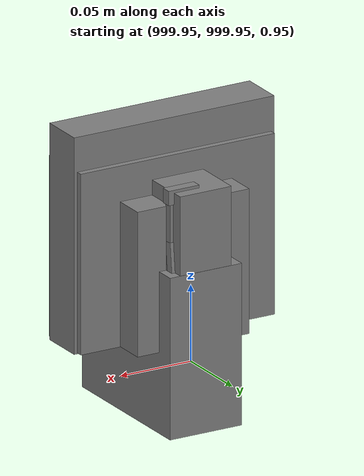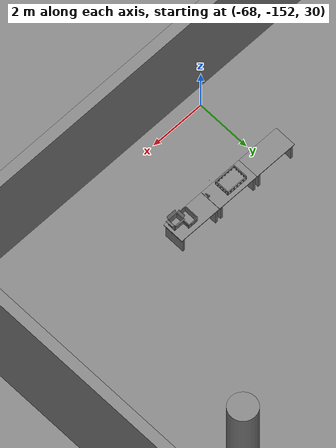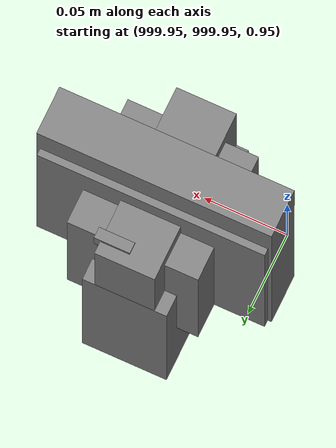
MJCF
<mujoco>
    <option gravity="0.000000000 0.000000000 -9.810000420" timestep="0.0049999999" integrator="implicitfast" density="1.225" viscosity="1.8000001e-05" noslip_iterations="10" iterations="100" sdf_iterations="50">
        <flag multiccd="disable"/>
    </option>
    <size memory="1000M"/>
    <compiler coordinate="local"/>
    <worldbody>
        <light cutoff="30" pos="0 1 1" dir="0 -1 -2"/>
        <light cutoff="30" pos="0 -1 1" dir="0 1 -2"/>
        <body pos="-64.866622925 -149.383972168 30.183746338" euler="89.999984741 89.999946594 0.000000000" name="openloong_gripper_2f85_fix_base_usda_bluebox_01">
            <geom contype="1" conaffinity="1" density="1000" type="box" material="" rgba="0.500000000 0.500000000 0.500000000 1.000000000" solimp="0.899999976 0.949999988 0.001000000" friction="1.000000000 0.005000000 0.000100000" solref="0.020000000 1.000000000" margin="0" condim="3" group="0" pos="0.276580811 0.187225342 0.000068665" quat="0.707106948 0.000077471 0.707106352 0.000077486" size="0.100000001 0.057999998 0.010000000" name="openloong_gripper_2f85_fix_base_usda_geom_48F5B2C0_1D15_4AD4_ABB2_C003ED0D4273"/>
            <geom contype="1" conaffinity="1" density="1000" type="box" material="" rgba="0.500000000 0.500000000 0.500000000 1.000000000" solimp="0.899999976 0.949999988 0.001000000" friction="1.000000000 0.005000000 0.000100000" solref="0.020000000 1.000000000" margin="0" condim="3" group="0" pos="0.000000000 0.002883911 0.000000000" quat="0.999999881 0.000000000 0.000000000 0.000000000" size="0.254000008 0.003000000 0.172000006" name="openloong_gripper_2f85_fix_base_usda_geom_6F7F98E7_3A60_4C84_B5B7_5B0E768F36E2"/>
            <geom contype="1" conaffinity="1" density="1000" type="box" material="" rgba="0.500000000 0.500000000 0.500000000 1.000000000" solimp="0.899999976 0.949999988 0.001000000" friction="1.000000000 0.005000000 0.000100000" solref="0.020000000 1.000000000" margin="0" condim="3" group="0" pos="0.000000000 0.124874115 0.173484802" quat="0.999796331 0.020176515 -0.000000015 0.000000030" size="0.259999990 0.119999997 0.007000000" name="openloong_gripper_2f85_fix_base_usda_geom_BD22D240_552C_445F_8D97_DCAA1D9BF025"/>
            <geom contype="1" conaffinity="1" density="1000" type="box" material="" rgba="0.500000000 0.500000000 0.500000000 1.000000000" solimp="0.899999976 0.949999988 0.001000000" friction="1.000000000 0.005000000 0.000100000" solref="0.020000000 1.000000000" margin="0" condim="3" group="0" pos="0.000000000 0.124874115 -0.173469543" quat="0.999796331 -0.020176545 -0.000000015 0.000000000" size="0.259999990 0.119999997 0.007000000" name="openloong_gripper_2f85_fix_base_usda_geom_33F26605_C299_4A0D_AAF4_429E6EC8F81C"/>
            <geom contype="1" conaffinity="1" density="1000" type="box" material="" rgba="0.500000000 0.500000000 0.500000000 1.000000000" solimp="0.899999976 0.949999988 0.001000000" friction="1.000000000 0.005000000 0.000100000" solref="0.020000000 1.000000000" margin="0" condim="3" group="0" pos="0.000000000 0.214008331 0.188980103" quat="0.999912977 0.013176724 0.000000015 0.000000000" size="0.259999990 0.029999999 0.012500000" name="openloong_gripper_2f85_fix_base_usda_geom_0E9DD5C9_A596_4941_A230_08AE5E6C68CA"/>
            <geom contype="1" conaffinity="1" density="1000" type="box" material="" rgba="0.500000000 0.500000000 0.500000000 1.000000000" solimp="0.899999976 0.949999988 0.001000000" friction="1.000000000 0.005000000 0.000100000" solref="0.020000000 1.000000000" margin="0" condim="3" group="0" pos="-0.258361816 0.125289917 0.001876831" quat="0.702796936 -0.020792112 0.710783124 0.020769298" size="0.189999998 0.119999997 0.009000000" name="openloong_gripper_2f85_fix_base_usda_geom_F84338CA_4F34_4FE9_AA39_D835320C8D3F"/>
            <geom contype="1" conaffinity="1" density="1000" type="box" material="" rgba="0.500000000 0.500000000 0.500000000 1.000000000" solimp="0.899999976 0.949999988 0.001000000" friction="1.000000000 0.005000000 0.000100000" solref="0.020000000 1.000000000" margin="0" condim="3" group="0" pos="0.000000000 0.214008331 -0.188980103" quat="0.999912977 -0.013176769 0.000000030 0.000000015" size="0.259999990 0.029999999 0.012500000" name="openloong_gripper_2f85_fix_base_usda_geom_BACFB023_F586_409A_9122_5BB4F10E27C5"/>
            <geom contype="1" conaffinity="1" density="1000" type="box" material="" rgba="0.500000000 0.500000000 0.500000000 1.000000000" solimp="0.899999976 0.949999988 0.001000000" friction="1.000000000 0.005000000 0.000100000" solref="0.020000000 1.000000000" margin="0" condim="3" group="0" pos="-0.276611328 0.187225342 0.000068665" quat="0.707106650 0.000077441 0.707106709 0.000077456" size="0.100000001 0.057999998 0.010000000" name="openloong_gripper_2f85_fix_base_usda_geom_0441ADD1_8245_410D_81A0_FE8E98DAFF2E"/>
            <geom contype="1" conaffinity="1" density="1000" type="box" material="" rgba="0.500000000 0.500000000 0.500000000 1.000000000" solimp="0.899999976 0.949999988 0.001000000" friction="1.000000000 0.005000000 0.000100000" solref="0.020000000 1.000000000" margin="0" condim="3" group="0" pos="0.258331299 0.125289917 0.001876831" quat="0.702851415 0.018856421 0.710823774 -0.019329369" size="0.189999998 0.119999997 0.009000000" name="openloong_gripper_2f85_fix_base_usda_geom_C7EA1E33_AE1A_45F2_B491_15ACA7BBD8DB"/>
            <freejoint name="openloong_gripper_2f85_fix_base_usda_bluebox_01_joint"/>
            <site size="0.005000000 0.005000000 0.005000000" rgba="0.500000000 0.500000000 0.500000000 1.000000000" pos="0.000000000 0.000000000 0.000000000" quat="0.999961913 0.008726534 0.000000000 0.000000000" group="0" type="sphere" name="openloong_gripper_2f85_fix_base_usda_bluebox_01site"/>
        </body>
        <body pos="-64.496299744 -149.491867065 30.235729218" euler="0.000000000 0.000000000 89.999946594" name="openloong_gripper_2f85_fix_base_usda_cardboardbox_01">
            <geom contype="1" conaffinity="1" density="1000" type="box" material="" rgba="0.500000000 0.500000000 0.500000000 1.000000000" solimp="0.899999976 0.949999988 0.001000000" friction="1.000000000 0.005000000 0.000100000" solref="0.020000000 1.000000000" margin="0" condim="3" group="0" pos="-0.003166199 -0.004086494 0.005052090" quat="1.000000000 0.000000000 0.000000000 0.000000000" size="0.142499998 0.177500010 0.005000000" name="openloong_gripper_2f85_fix_base_usda_geom_704E7A8C_ADB3_4021_9E5B_8C8728BB6512"/>
            <geom contype="1" conaffinity="1" density="1000" type="box" material="" rgba="0.500000000 0.500000000 0.500000000 1.000000000" solimp="0.899999976 0.949999988 0.001000000" friction="1.000000000 0.005000000 0.000100000" solref="0.020000000 1.000000000" margin="0" condim="3" group="0" pos="-0.003166199 0.170316696 0.150570869" quat="1.000000000 0.000000000 0.000000000 0.000000000" size="0.142499998 0.005000000 0.149999991" name="openloong_gripper_2f85_fix_base_usda_geom_95D3099A_49E4_4711_A7AF_7B6363A676C0"/>
            <geom contype="1" conaffinity="1" density="1000" type="box" material="" rgba="0.500000000 0.500000000 0.500000000 1.000000000" solimp="0.899999976 0.949999988 0.001000000" friction="1.000000000 0.005000000 0.000100000" solref="0.020000000 1.000000000" margin="0" condim="3" group="0" pos="-0.147399902 -0.005307198 0.150570869" quat="1.000000000 0.000000000 0.000000000 0.000000000" size="0.005000000 0.177500010 0.149999991" name="openloong_gripper_2f85_fix_base_usda_geom_DB974831_956F_405D_B1C3_4023ED0DE5EB"/>
            <geom contype="1" conaffinity="1" density="1000" type="box" material="" rgba="0.500000000 0.500000000 0.500000000 1.000000000" solimp="0.899999976 0.949999988 0.001000000" friction="1.000000000 0.005000000 0.000100000" solref="0.020000000 1.000000000" margin="0" condim="3" group="0" pos="0.140275955 -0.005307198 0.150570869" quat="1.000000000 0.000000000 0.000000000 0.000000000" size="0.005000000 0.177500010 0.149999991" name="openloong_gripper_2f85_fix_base_usda_geom_E536223F_F6C3_48DF_ADC6_96774BC3CB86"/>
            <geom contype="1" conaffinity="1" density="1000" type="box" material="" rgba="0.500000000 0.500000000 0.500000000 1.000000000" solimp="0.899999976 0.949999988 0.001000000" friction="1.000000000 0.005000000 0.000100000" solref="0.020000000 1.000000000" margin="0" condim="3" group="0" pos="-0.003166199 -0.181550980 0.150570869" quat="1.000000000 0.000000000 0.000000000 0.000000000" size="0.142499998 0.005000000 0.149999991" name="openloong_gripper_2f85_fix_base_usda_geom_10371AA3_BE84_4256_9353_9CF22EAC5898"/>
            <freejoint name="openloong_gripper_2f85_fix_base_usda_cardboardbox_01_joint"/>
            <site size="0.005000000 0.005000000 0.005000000" rgba="0.500000000 0.500000000 0.500000000 1.000000000" pos="0.000000000 0.000000000 0.000000000" quat="0.999961913 0.008726535 0.000000000 0.000000000" group="0" type="sphere" name="openloong_gripper_2f85_fix_base_usda_site_2CCAF164_CA1A_4235_AAD6_95C7EECB0370"/>
            <body pos="0.139160156 -0.004048347 0.301930904" euler="-179.999954224 49.383502960 179.999954224" name="openloong_gripper_2f85_fix_base_usda_A1_006">
                <geom contype="1" conaffinity="1" density="1000" type="box" material="" rgba="0.500000000 0.500000000 0.500000000 1.000000000" solimp="0.899999976 0.949999988 0.001000000" friction="1.000000000 0.005000000 0.000100000" solref="0.020000000 1.000000000" margin="0" condim="3" group="0" pos="-0.071587563 0.000009537 0.001745224" quat="0.999999881 0.000000000 0.000000000 0.000000000" size="0.071249999 0.179999992 0.002500000" name="openloong_gripper_2f85_fix_base_usda_geom_729C663D_A4F5_4441_994C_5978C662C793"/>
                <joint armature="0" stiffness="0.07" damping="0.0099999998" axis="0.000000 1.000000 0.000000" type="hinge" name="openloong_gripper_2f85_fix_base_usda_A1_006"/>
            </body>
            <body pos="-0.145902634 -0.004086494 0.301938057" euler="-180.000000000 -60.000011444 -180.000000000" name="openloong_gripper_2f85_fix_base_usda_A2_006">
                <geom contype="1" conaffinity="1" density="1000" type="box" material="" rgba="0.500000000 0.500000000 0.500000000 1.000000000" solimp="0.899999976 0.949999988 0.001000000" friction="1.000000000 0.005000000 0.000100000" solref="0.020000000 1.000000000" margin="0" condim="3" group="0" pos="0.071268082 0.000009537 0.002717972" quat="0.000002921 0.000000000 -0.000000030 0.999999881" size="0.071249999 0.179999992 0.002500000" name="openloong_gripper_2f85_fix_base_usda_geom_2F88EC6E_BF5C_484E_97A9_A0CD7EAAD7A7"/>
                <joint armature="0" stiffness="0.07" damping="0.0099999998" axis="0.000000 1.000000 0.000000" type="hinge" name="openloong_gripper_2f85_fix_base_usda_A2_006"/>
            </body>
            <body pos="-0.003385544 0.175991058 0.301930904" euler="-125.858116150 -0.000004561 0.000002331" name="openloong_gripper_2f85_fix_base_usda_B2_006">
                <geom contype="1" conaffinity="1" density="1000" type="box" material="" rgba="0.500000000 0.500000000 0.500000000 1.000000000" solimp="0.899999976 0.949999988 0.001000000" friction="1.000000000 0.005000000 0.000100000" solref="0.020000000 1.000000000" margin="0" condim="3" group="0" pos="0.000009537 -0.070939064 -0.002470016" quat="0.999614120 0.027776197 -0.000000015 0.000000030" size="0.137500003 0.064999998 0.005000000" name="openloong_gripper_2f85_fix_base_usda_geom_D3CAD112_C9F9_4F29_A236_B5C4F1F271A5"/>
                <joint armature="0" stiffness="0.07" damping="0.0099999998" axis="1.000000 0.000000 0.000000" type="hinge" name="openloong_gripper_2f85_fix_base_usda_B2_006"/>
            </body>
            <body pos="-0.003385544 -0.184140205 0.301938057" euler="147.805557251 0.000000000 0.000000000" name="openloong_gripper_2f85_fix_base_usda_B1_006">
                <geom contype="1" conaffinity="1" density="1000" type="box" material="" rgba="0.500000000 0.500000000 0.500000000 1.000000000" solimp="0.899999976 0.949999988 0.001000000" friction="1.000000000 0.005000000 0.000100000" solref="0.020000000 1.000000000" margin="0" condim="3" group="0" pos="-0.000028610 0.070202351 -0.002703667" quat="0.999614179 -0.027776167 0.000000000 0.000000000" size="0.137500003 0.064999998 0.005000000" name="openloong_gripper_2f85_fix_base_usda_geom_F0D115D4_D817_448D_ACCA_0ABB1B5415E3"/>
                <joint armature="0" stiffness="0.07" damping="0.0099999998" axis="1.000000 0.000000 0.000000" type="hinge" name="openloong_gripper_2f85_fix_base_usda_B1_006"/>
            </body>
        </body>
        <body pos="-65.882858276 -149.481979370 30.229999542" euler="-64.487716675 0.000000000 0.000000000" name="openloong_gripper_2f85_fix_base_usda_Barcode">
            <geom contype="1" conaffinity="1" density="1000" type="box" material="" rgba="0.500000000 0.500000000 0.500000000 1.000000000" solimp="0.899999976 0.949999988 0.001000000" friction="1.000000000 0.005000000 0.000100000" solref="0.020000000 1.000000000" margin="0" condim="3" group="0" pos="0.000000000 0.013038635 0.001419067" quat="0.000000000 0.000000000 0.000000000 1.000000119" size="0.034000002 0.010000000 0.017999999" name="openloong_gripper_2f85_fix_base_usda_geom_DAC1988B_5B4C_42D8_AE6F_89219FDA32AC"/>
            <geom contype="1" conaffinity="1" density="1000" type="box" material="" rgba="0.500000000 0.500000000 0.500000000 1.000000000" solimp="0.899999976 0.949999988 0.001000000" friction="1.000000000 0.005000000 0.000100000" solref="0.020000000 1.000000000" margin="0" condim="3" group="0" pos="0.000000000 -0.035301208 -0.007095337" quat="0.000000000 0.000000000 -0.043619365 0.999048233" size="0.028999999 0.010000000 0.020000000" name="openloong_gripper_2f85_fix_base_usda_geom_323B9980_B235_4CD4_9996_751CE74A9DD3"/>
            <geom contype="1" conaffinity="1" density="1000" type="box" material="" rgba="0.500000000 0.500000000 0.500000000 1.000000000" solimp="0.899999976 0.949999988 0.001000000" friction="1.000000000 0.005000000 0.000100000" solref="0.020000000 1.000000000" margin="0" condim="3" group="0" pos="0.000000000 -0.043411255 -0.011749268" quat="0.922262907 0.386563420 0.000000000 0.000000000" size="0.026000001 0.010000000 0.020000000" name="openloong_gripper_2f85_fix_base_usda_geom_D5087671_BC8F_4317_82B3_B7459B70AE98"/>
            <geom contype="1" conaffinity="1" density="1000" type="box" material="" rgba="0.500000000 0.500000000 0.500000000 1.000000000" solimp="0.899999976 0.949999988 0.001000000" friction="1.000000000 0.005000000 0.000100000" solref="0.020000000 1.000000000" margin="0" condim="3" group="0" pos="0.000000000 -0.016967773 -0.031860352" quat="0.000000000 0.000000000 0.000000000 1.000000119" size="0.008000000 0.010000000 0.013000000" name="openloong_gripper_2f85_fix_base_usda_geom_800EEBCE_C2CE_4C0B_B345_16A2D8E2C116"/>
            <geom contype="1" conaffinity="1" density="1000" type="box" material="" rgba="0.500000000 0.500000000 0.500000000 1.000000000" solimp="0.899999976 0.949999988 0.001000000" friction="1.000000000 0.005000000 0.000100000" solref="0.020000000 1.000000000" margin="0" condim="3" group="0" pos="0.000000000 -0.001869202 0.000312805" quat="0.953716993 0.300705761 0.000000000 0.000000000" size="0.032000002 0.010000000 0.018999999" name="openloong_gripper_2f85_fix_base_usda_geom_CE45B450_9DFA_42A5_BC19_64B41A28CB92"/>
            <geom contype="1" conaffinity="1" density="1000" type="box" material="" rgba="0.500000000 0.500000000 0.500000000 1.000000000" solimp="0.899999976 0.949999988 0.001000000" friction="1.000000000 0.005000000 0.000100000" solref="0.020000000 1.000000000" margin="0" condim="3" group="0" pos="0.000000000 -0.019531250 -0.003173828" quat="0.953716993 0.300705761 0.000000000 0.000000000" size="0.030999999 0.010000000 0.020000000" name="openloong_gripper_2f85_fix_base_usda_geom_FDB66AF8_D517_461B_A0F7_97E01D1698AD"/>
            <geom contype="1" conaffinity="1" density="1000" type="box" material="" rgba="0.500000000 0.500000000 0.500000000 1.000000000" solimp="0.899999976 0.949999988 0.001000000" friction="1.000000000 0.005000000 0.000100000" solref="0.020000000 1.000000000" margin="0" condim="3" group="0" pos="0.000000000 -0.035301208 -0.007095337" quat="0.953716993 0.300705761 0.000000000 0.000000000" size="0.028999999 0.010000000 0.020000000" name="openloong_gripper_2f85_fix_base_usda_geom_70F7B98A_94AE_4F11_8FDF_528DC796CDFA"/>
            <geom contype="1" conaffinity="1" density="1000" type="box" material="" rgba="0.500000000 0.500000000 0.500000000 1.000000000" solimp="0.899999976 0.949999988 0.001000000" friction="1.000000000 0.005000000 0.000100000" solref="0.020000000 1.000000000" margin="0" condim="3" group="0" pos="0.000000000 -0.042617798 -0.071121216" quat="0.000000000 0.000000000 0.000000000 1.000000119" size="0.013000000 0.021000000 0.059999999" name="openloong_gripper_2f85_fix_base_usda_geom_A523C0A4_8363_4A93_81DE_8867C7E4FA1D"/>
            <freejoint name="openloong_gripper_2f85_fix_base_usda_Barcode_joint"/>
            <site size="0.005000000 0.005000000 0.005000000" rgba="0.500000000 0.500000000 0.500000000 1.000000000" pos="0.000000000 0.000000000 0.000000000" quat="1.000000000 0.000000000 0.000000000 0.000000000" group="0" type="sphere" name="openloong_gripper_2f85_fix_base_usda_Barcode_site"/>
        </body>
        <body pos="-66.745018005 -149.392349243 30.184000015" euler="0.000000000 0.000000000 89.999946594" name="[22332791601905]_Basket_01">
            <geom contype="1" conaffinity="1" density="1000" type="box" material="" rgba="0.500000000 0.500000000 0.500000000 1.000000000" solimp="0.899999976 0.949999988 0.001000000" friction="1.000000000 0.005000000 0.000100000" solref="0.020000000 1.000000000" margin="0" condim="3" group="0" pos="-0.052425385 0.389207840 0.089787483" quat="0.707107008 0.000000000 0.000000000 0.707106411" size="0.014249999 0.014249999 0.059999999" name="[22332791601905]_geom_7A9E25DC_11C1_451D_8304_7169C1AD2E04"/>
            <geom contype="1" conaffinity="1" density="1000" type="box" material="" rgba="0.500000000 0.500000000 0.500000000 1.000000000" solimp="0.899999976 0.949999988 0.001000000" friction="1.000000000 0.005000000 0.000100000" solref="0.020000000 1.000000000" margin="0" condim="3" group="0" pos="0.264015198 -0.133043289 0.089787483" quat="0.707107008 0.000000000 0.000000000 0.707106411" size="0.014249999 0.014249999 0.059999999" name="[22332791601905]_geom_A7741A04_DB93_4363_B55A_044FEB118872"/>
            <geom contype="1" conaffinity="1" density="1000" type="box" material="" rgba="0.500000000 0.500000000 0.500000000 1.000000000" solimp="0.899999976 0.949999988 0.001000000" friction="1.000000000 0.005000000 0.000100000" solref="0.020000000 1.000000000" margin="0" condim="3" group="0" pos="-0.264015198 -0.265548706 0.089793205" quat="0.707107008 0.000000000 0.000000000 0.707106411" size="0.014249999 0.014249999 0.059999999" name="[22332791601905]_geom_39D59B15_D34D_44AD_9E60_10FE0AFBC429"/>
            <geom contype="1" conaffinity="1" density="1000" type="box" material="" rgba="0.500000000 0.500000000 0.500000000 1.000000000" solimp="0.899999976 0.949999988 0.001000000" friction="1.000000000 0.005000000 0.000100000" solref="0.020000000 1.000000000" margin="0" condim="3" group="0" pos="-0.160263062 -0.389322281 0.089793205" quat="0.707107008 0.000000000 0.000000000 0.707106411" size="0.014249999 0.014249999 0.059999999" name="[22332791601905]_geom_BE0A1030_8BA7_460C_B72A_01D55D52BC9C"/>
            <geom contype="1" conaffinity="1" density="1000" type="box" material="" rgba="0.500000000 0.500000000 0.500000000 1.000000000" solimp="0.899999976 0.949999988 0.001000000" friction="1.000000000 0.005000000 0.000100000" solref="0.020000000 1.000000000" margin="0" condim="3" group="0" pos="0.162265778 -0.389322281 0.089787483" quat="0.707107008 0.000000000 0.000000000 0.707106411" size="0.014249999 0.014249999 0.059999999" name="[22332791601905]_geom_A46EF1BE_0B71_424F_8CB1_32223CC7541A"/>
            <geom contype="1" conaffinity="1" density="1000" type="box" material="" rgba="0.500000000 0.500000000 0.500000000 1.000000000" solimp="0.899999976 0.949999988 0.001000000" friction="1.000000000 0.005000000 0.000100000" solref="0.020000000 1.000000000" margin="0" condim="3" group="0" pos="0.264015198 0.389207840 0.089787483" quat="0.707107008 0.000000000 0.000000000 0.707106411" size="0.014249999 0.014249999 0.059999999" name="[22332791601905]_geom_C9274284_022C_40E4_95B8_42885128A308"/>
            <geom contype="1" conaffinity="1" density="1000" type="box" material="" rgba="0.500000000 0.500000000 0.500000000 1.000000000" solimp="0.899999976 0.949999988 0.001000000" friction="1.000000000 0.005000000 0.000100000" solref="0.020000000 1.000000000" margin="0" condim="3" group="0" pos="-0.264015198 -0.133043289 0.089793205" quat="0.707107008 0.000000000 0.000000000 0.707106411" size="0.014249999 0.014249999 0.059999999" name="[22332791601905]_geom_2F826FAD_DE41_4236_8986_C89C729C2E12"/>
            <geom contype="1" conaffinity="1" density="1000" type="box" material="" rgba="0.500000000 0.500000000 0.500000000 1.000000000" solimp="0.899999976 0.949999988 0.001000000" friction="1.000000000 0.005000000 0.000100000" solref="0.020000000 1.000000000" margin="0" condim="3" group="0" pos="-0.264026642 0.269256592 0.089793205" quat="0.707107008 0.000000000 0.000000000 0.707106411" size="0.014249999 0.014249999 0.059999999" name="[22332791601905]_geom_5C57AE9F_1DEB_4FEA_8207_80E9D5211101"/>
            <geom contype="1" conaffinity="1" density="1000" type="box" material="" rgba="0.500000000 0.500000000 0.500000000 1.000000000" solimp="0.899999976 0.949999988 0.001000000" friction="1.000000000 0.005000000 0.000100000" solref="0.020000000 1.000000000" margin="0" condim="3" group="0" pos="0.054462433 0.389207840 0.089787483" quat="0.707107008 0.000000000 0.000000000 0.707106411" size="0.014249999 0.014249999 0.059999999" name="[22332791601905]_geom_0F8A7FB7_682A_43C7_B7F9_901431F7691A"/>
            <geom contype="1" conaffinity="1" density="1000" type="box" material="" rgba="0.500000000 0.500000000 0.500000000 1.000000000" solimp="0.899999976 0.949999988 0.001000000" friction="1.000000000 0.005000000 0.000100000" solref="0.020000000 1.000000000" margin="0" condim="3" group="0" pos="0.054462433 -0.389322281 0.089787483" quat="0.707107008 0.000000000 0.000000000 0.707106411" size="0.014249999 0.014249999 0.059999999" name="[22332791601905]_geom_3AF376F9_52E8_4D40_8232_0FE6AC15833E"/>
            <geom contype="1" conaffinity="1" density="1000" type="box" material="" rgba="0.500000000 0.500000000 0.500000000 1.000000000" solimp="0.899999976 0.949999988 0.001000000" friction="1.000000000 0.005000000 0.000100000" solref="0.020000000 1.000000000" margin="0" condim="3" group="0" pos="0.264015198 0.269256592 0.089793205" quat="0.707107008 0.000000000 0.000000000 0.707106411" size="0.014249999 0.014249999 0.059999999" name="[22332791601905]_geom_422CCC36_9B0D_401D_9850_19EE11D3F552"/>
            <geom contype="1" conaffinity="1" density="1000" type="box" material="" rgba="0.500000000 0.500000000 0.500000000 1.000000000" solimp="0.899999976 0.949999988 0.001000000" friction="1.000000000 0.005000000 0.000100000" solref="0.020000000 1.000000000" margin="0" condim="3" group="0" pos="0.264015198 -0.389322281 0.089787483" quat="0.707107008 0.000000000 0.000000000 0.707106411" size="0.014249999 0.014249999 0.059999999" name="[22332791601905]_geom_CA7F54B4_350E_40F7_83FE_958D53A851B8"/>
            <geom contype="1" conaffinity="1" density="1000" type="box" material="" rgba="0.500000000 0.500000000 0.500000000 1.000000000" solimp="0.899999976 0.949999988 0.001000000" friction="1.000000000 0.005000000 0.000100000" solref="0.020000000 1.000000000" margin="0" condim="3" group="0" pos="0.000000000 0.000000000 0.015998840" quat="0.707107008 0.000000000 0.000000000 0.707106411" size="0.403499991 0.279000014 0.015750000" name="[22332791601905]_geom_E5C6FD35_EEE2_433D_B62F_504A94B6436B"/>
            <geom contype="1" conaffinity="1" density="1000" type="box" material="" rgba="0.500000000 0.500000000 0.500000000 1.000000000" solimp="0.899999976 0.949999988 0.001000000" friction="1.000000000 0.005000000 0.000100000" solref="0.020000000 1.000000000" margin="0" condim="3" group="0" pos="0.000000000 -0.389476776 0.163619041" quat="0.707107008 0.000000000 0.000000000 0.707106411" size="0.015000000 0.277500004 0.015750000" name="[22332791601905]_geom_F7C0BBE5_83DE_4264_A45B_405B03B7C0D4"/>
            <geom contype="1" conaffinity="1" density="1000" type="box" material="" rgba="0.500000000 0.500000000 0.500000000 1.000000000" solimp="0.899999976 0.949999988 0.001000000" friction="1.000000000 0.005000000 0.000100000" solref="0.020000000 1.000000000" margin="0" condim="3" group="0" pos="0.162265778 0.389207840 0.089787483" quat="0.707107008 0.000000000 0.000000000 0.707106411" size="0.014249999 0.014249999 0.059999999" name="[22332791601905]_geom_1450FEEE_0435_4754_BCFA_3DEFDC014AF5"/>
            <geom contype="1" conaffinity="1" density="1000" type="box" material="" rgba="0.500000000 0.500000000 0.500000000 1.000000000" solimp="0.899999976 0.949999988 0.001000000" friction="1.000000000 0.005000000 0.000100000" solref="0.020000000 1.000000000" margin="0" condim="3" group="0" pos="0.000000000 0.389471054 0.163619041" quat="0.707107008 0.000000000 0.000000000 0.707106411" size="0.015000000 0.277500004 0.015750000" name="[22332791601905]_geom_C9632094_59B9_4072_A872_F3737F7E0B86"/>
            <geom contype="1" conaffinity="1" density="1000" type="box" material="" rgba="0.500000000 0.500000000 0.500000000 1.000000000" solimp="0.899999976 0.949999988 0.001000000" friction="1.000000000 0.005000000 0.000100000" solref="0.020000000 1.000000000" margin="0" condim="3" group="0" pos="-0.263511658 0.000000000 0.163619041" quat="0.707107008 0.000000000 0.000000000 0.707106411" size="0.403499991 0.015000000 0.015750000" name="[22332791601905]_geom_E6293181_4B7D_44FA_9D6F_751945E790EF"/>
            <geom contype="1" conaffinity="1" density="1000" type="box" material="" rgba="0.500000000 0.500000000 0.500000000 1.000000000" solimp="0.899999976 0.949999988 0.001000000" friction="1.000000000 0.005000000 0.000100000" solref="0.020000000 1.000000000" margin="0" condim="3" group="0" pos="-0.264015198 0.141334534 0.089793205" quat="0.707107008 0.000000000 0.000000000 0.707106411" size="0.014249999 0.014249999 0.059999999" name="[22332791601905]_geom_D5367BF9_E81B_475D_B4EF_0C3DFA3D1F54"/>
            <geom contype="1" conaffinity="1" density="1000" type="box" material="" rgba="0.500000000 0.500000000 0.500000000 1.000000000" solimp="0.899999976 0.949999988 0.001000000" friction="1.000000000 0.005000000 0.000100000" solref="0.020000000 1.000000000" margin="0" condim="3" group="0" pos="0.264015198 -0.265548706 0.089787483" quat="0.707107008 0.000000000 0.000000000 0.707106411" size="0.014249999 0.014249999 0.059999999" name="[22332791601905]_geom_980F5953_40D9_4CD3_B3DA_00558AFB4BE8"/>
            <geom contype="1" conaffinity="1" density="1000" type="box" material="" rgba="0.500000000 0.500000000 0.500000000 1.000000000" solimp="0.899999976 0.949999988 0.001000000" friction="1.000000000 0.005000000 0.000100000" solref="0.020000000 1.000000000" margin="0" condim="3" group="0" pos="-0.160263062 0.389207840 0.089787483" quat="0.707107008 0.000000000 0.000000000 0.707106411" size="0.014249999 0.014249999 0.059999999" name="[22332791601905]_geom_584537C0_64A2_49CB_8F2A_A87D10B1DFB4"/>
            <geom contype="1" conaffinity="1" density="1000" type="box" material="" rgba="0.500000000 0.500000000 0.500000000 1.000000000" solimp="0.899999976 0.949999988 0.001000000" friction="1.000000000 0.005000000 0.000100000" solref="0.020000000 1.000000000" margin="0" condim="3" group="0" pos="-0.052425385 -0.389322281 0.089787483" quat="0.707107008 0.000000000 0.000000000 0.707106411" size="0.014249999 0.014249999 0.059999999" name="[22332791601905]_geom_5A520550_AD0E_42DC_A373_88C520FE55BD"/>
            <geom contype="1" conaffinity="1" density="1000" type="box" material="" rgba="0.500000000 0.500000000 0.500000000 1.000000000" solimp="0.899999976 0.949999988 0.001000000" friction="1.000000000 0.005000000 0.000100000" solref="0.020000000 1.000000000" margin="0" condim="3" group="0" pos="-0.264026642 -0.389322281 0.089793205" quat="0.707107008 0.000000000 0.000000000 0.707106411" size="0.014249999 0.014249999 0.059999999" name="[22332791601905]_geom_2E4D8066_7A01_431E_98DD_27EAACDCC5E3"/>
            <geom contype="1" conaffinity="1" density="1000" type="box" material="" rgba="0.500000000 0.500000000 0.500000000 1.000000000" solimp="0.899999976 0.949999988 0.001000000" friction="1.000000000 0.005000000 0.000100000" solref="0.020000000 1.000000000" margin="0" condim="3" group="0" pos="0.264015198 0.141334534 0.089787483" quat="0.707107008 0.000000000 0.000000000 0.707106411" size="0.014249999 0.014249999 0.059999999" name="[22332791601905]_geom_354FE579_0852_403C_AF7F_71DDB1209E2C"/>
            <geom contype="1" conaffinity="1" density="1000" type="box" material="" rgba="0.500000000 0.500000000 0.500000000 1.000000000" solimp="0.899999976 0.949999988 0.001000000" friction="1.000000000 0.005000000 0.000100000" solref="0.020000000 1.000000000" margin="0" condim="3" group="0" pos="-0.264015198 0.389207840 0.089793205" quat="0.707107008 0.000000000 0.000000000 0.707106411" size="0.014249999 0.014249999 0.059999999" name="[22332791601905]_geom_322CF71A_8A04_4B7A_8A4E_81B024917006"/>
            <geom contype="1" conaffinity="1" density="1000" type="box" material="" rgba="0.500000000 0.500000000 0.500000000 1.000000000" solimp="0.899999976 0.949999988 0.001000000" friction="1.000000000 0.005000000 0.000100000" solref="0.020000000 1.000000000" margin="0" condim="3" group="0" pos="0.264015198 0.004480362 0.089787483" quat="0.707107008 0.000000000 0.000000000 0.707106411" size="0.014249999 0.014249999 0.059999999" name="[22332791601905]_geom_7435AA67_5F36_4459_BC70_990CDC7BCD9F"/>
            <geom contype="1" conaffinity="1" density="1000" type="box" material="" rgba="0.500000000 0.500000000 0.500000000 1.000000000" solimp="0.899999976 0.949999988 0.001000000" friction="1.000000000 0.005000000 0.000100000" solref="0.020000000 1.000000000" margin="0" condim="3" group="0" pos="0.263694763 -0.000011444 0.163619041" quat="0.707107008 0.000000000 0.000000000 0.707106411" size="0.403499991 0.015000000 0.015750000" name="[22332791601905]_geom_E4DF4AEA_0BA5_40A7_BA99_AABA382784CE"/>
            <geom contype="1" conaffinity="1" density="1000" type="box" material="" rgba="0.500000000 0.500000000 0.500000000 1.000000000" solimp="0.899999976 0.949999988 0.001000000" friction="1.000000000 0.005000000 0.000100000" solref="0.020000000 1.000000000" margin="0" condim="3" group="0" pos="-0.264015198 0.004480362 0.089793205" quat="0.707107008 0.000000000 0.000000000 0.707106411" size="0.014249999 0.014249999 0.059999999" name="[22332791601905]_geom_4C72DFFA_6A58_4F4D_B3BF_2D649C26F7EA"/>
            <freejoint name="[22332791601905]_joint_6392A413_F0DB_4BC2_A217_B514CECC8725"/>
        </body>
        <body pos="0.000000000 0.000000000 0.000000000" euler="0.000000000 0.000000000 0.000000000" name="Static Objects_Static Objects">
            <geom contype="1" conaffinity="1" density="1000" type="box" material="" rgba="0.500000000 0.500000000 0.500000000 1.000000000" solimp="0.899999976 0.949999988 0.001000000" friction="1.000000000 0.005000000 0.000100000" solref="0.020000000 1.000000000" margin="0" condim="3" group="0" pos="-67.544113159 -149.365814209 29.727830887" quat="0.500000417 0.499999970 0.499999553 0.499999970" size="0.381000012 0.319999993 0.041000001" name="Static Objects_geom_05BCB1F0_9E11_427D_9FD3_4F8F7B68E86D"/>
            <geom contype="1" conaffinity="1" density="1000" type="box" material="" rgba="0.500000000 0.500000000 0.500000000 1.000000000" solimp="0.899999976 0.949999988 0.001000000" friction="1.000000000 0.005000000 0.000100000" solref="0.020000000 1.000000000" margin="0" condim="3" group="0" pos="-68.239501953 -149.365814209 30.086868286" quat="0.500000417 0.499999970 0.499999553 0.499999970" size="0.370999992 0.039500002 0.745000005" name="Static Objects_geom_1188C2A8_6639_4D15_BD8B_CBA701F52DC5"/>
            <geom contype="1" conaffinity="1" density="1000" type="box" material="" rgba="0.500000000 0.500000000 0.500000000 1.000000000" solimp="0.899999976 0.949999988 0.001000000" friction="1.000000000 0.005000000 0.000100000" solref="0.020000000 1.000000000" margin="0" condim="3" group="0" pos="-68.239501953 -149.365814209 30.147235870" quat="0.500000417 0.499999970 0.499999553 0.499999970" size="0.400000006 0.022000000 0.800000012" name="Static Objects_geom_6A3A26D9_A81F_4A04_9F65_EE546BD7CBFD"/>
            <geom contype="1" conaffinity="1" density="1000" type="box" material="" rgba="0.500000000 0.500000000 0.500000000 1.000000000" solimp="0.899999976 0.949999988 0.001000000" friction="1.000000000 0.005000000 0.000100000" solref="0.020000000 1.000000000" margin="0" condim="3" group="0" pos="-68.934890747 -149.365814209 29.727830887" quat="0.500000417 0.499999970 0.499999553 0.499999970" size="0.381000012 0.319999993 0.041000001" name="Static Objects_geom_4F5635E2_E768_43A8_923C_AC0C3DA0C11D"/>
            <geom contype="1" conaffinity="1" density="1000" type="box" material="" rgba="0.500000000 0.500000000 0.500000000 1.000000000" solimp="0.899999976 0.949999988 0.001000000" friction="1.000000000 0.005000000 0.000100000" solref="0.020000000 1.000000000" margin="0" condim="3" group="0" pos="-68.239501953 -149.365814209 29.561563492" quat="0.500000417 0.499999970 0.499999553 0.499999970" size="0.020000000 0.022000000 0.660000026" name="Static Objects_geom_795890F5_DFC9_4C4C_BB2E_77A901E05D4D"/>
            <geom contype="1" conaffinity="1" density="1000" type="box" material="" rgba="0.500000000 0.500000000 0.500000000 1.000000000" solimp="0.899999976 0.949999988 0.001000000" friction="1.000000000 0.005000000 0.000100000" solref="0.020000000 1.000000000" margin="0" condim="3" group="0" pos="-65.945671082 -149.365814209 29.727830887" quat="0.500000417 0.499999970 0.499999553 0.499999970" size="0.381000012 0.319999993 0.041000001" name="Static Objects_geom_C6067823_4692_439E_88B0_FC53C71EADA2"/>
            <geom contype="1" conaffinity="1" density="1000" type="box" material="" rgba="0.500000000 0.500000000 0.500000000 1.000000000" solimp="0.899999976 0.949999988 0.001000000" friction="1.000000000 0.005000000 0.000100000" solref="0.020000000 1.000000000" margin="0" condim="3" group="0" pos="-66.641059875 -149.365814209 30.086868286" quat="0.500000417 0.499999970 0.499999553 0.499999970" size="0.370999992 0.039500002 0.745000005" name="Static Objects_geom_09ABB7E8_CD07_41B4_B368_D63B17DDFF63"/>
            <geom contype="1" conaffinity="1" density="1000" type="box" material="" rgba="0.500000000 0.500000000 0.500000000 1.000000000" solimp="0.899999976 0.949999988 0.001000000" friction="1.000000000 0.005000000 0.000100000" solref="0.020000000 1.000000000" margin="0" condim="3" group="0" pos="-66.641059875 -149.365814209 30.147235870" quat="0.500000417 0.499999970 0.499999553 0.499999970" size="0.400000006 0.022000000 0.800000012" name="Static Objects_geom_A8281D10_332C_451A_9EEA_25098E676149"/>
            <geom contype="1" conaffinity="1" density="1000" type="box" material="" rgba="0.500000000 0.500000000 0.500000000 1.000000000" solimp="0.899999976 0.949999988 0.001000000" friction="1.000000000 0.005000000 0.000100000" solref="0.020000000 1.000000000" margin="0" condim="3" group="0" pos="-67.336448669 -149.365814209 29.727830887" quat="0.500000417 0.499999970 0.499999553 0.499999970" size="0.381000012 0.319999993 0.041000001" name="Static Objects_geom_CDB25F78_8978_48D1_B705_02A6A829E950"/>
            <geom contype="1" conaffinity="1" density="1000" type="box" material="" rgba="0.500000000 0.500000000 0.500000000 1.000000000" solimp="0.899999976 0.949999988 0.001000000" friction="1.000000000 0.005000000 0.000100000" solref="0.020000000 1.000000000" margin="0" condim="3" group="0" pos="-66.641059875 -149.365814209 29.561563492" quat="0.500000417 0.499999970 0.499999553 0.499999970" size="0.020000000 0.022000000 0.660000026" name="Static Objects_geom_1FE1DABB_4F33_462E_B43F_9492B7843876"/>
            <geom contype="1" conaffinity="1" density="1000" type="box" material="" rgba="0.500000000 0.500000000 0.500000000 1.000000000" solimp="0.899999976 0.949999988 0.001000000" friction="1.000000000 0.005000000 0.000100000" solref="0.020000000 1.000000000" margin="0" condim="3" group="0" pos="-64.338577271 -149.365814209 29.727830887" quat="0.500000417 0.499999970 0.499999553 0.499999970" size="0.381000012 0.319999993 0.041000001" name="Static Objects_geom_46E940D3_036D_42B5_8773_88CCFB26B0E6"/>
            <geom contype="1" conaffinity="1" density="1000" type="box" material="" rgba="0.500000000 0.500000000 0.500000000 1.000000000" solimp="0.899999976 0.949999988 0.001000000" friction="1.000000000 0.005000000 0.000100000" solref="0.020000000 1.000000000" margin="0" condim="3" group="0" pos="-65.033966064 -149.365814209 30.086868286" quat="0.500000417 0.499999970 0.499999553 0.499999970" size="0.370999992 0.039500002 0.745000005" name="Static Objects_geom_FE72BE75_D248_4D55_AC9A_32C02C4BD42C"/>
            <geom contype="1" conaffinity="1" density="1000" type="box" material="" rgba="0.500000000 0.500000000 0.500000000 1.000000000" solimp="0.899999976 0.949999988 0.001000000" friction="1.000000000 0.005000000 0.000100000" solref="0.020000000 1.000000000" margin="0" condim="3" group="0" pos="-65.033966064 -149.365814209 30.147235870" quat="0.500000417 0.499999970 0.499999553 0.499999970" size="0.400000006 0.022000000 0.800000012" name="Static Objects_geom_F79B11F7_4220_4FC2_8F3D_3C795F128009"/>
            <geom contype="1" conaffinity="1" density="1000" type="box" material="" rgba="0.500000000 0.500000000 0.500000000 1.000000000" solimp="0.899999976 0.949999988 0.001000000" friction="1.000000000 0.005000000 0.000100000" solref="0.020000000 1.000000000" margin="0" condim="3" group="0" pos="-65.729354858 -149.365814209 29.727830887" quat="0.500000417 0.499999970 0.499999553 0.499999970" size="0.381000012 0.319999993 0.041000001" name="Static Objects_geom_624572A5_A455_4584_8211_1B2615D361C9"/>
            <geom contype="1" conaffinity="1" density="1000" type="box" material="" rgba="0.500000000 0.500000000 0.500000000 1.000000000" solimp="0.899999976 0.949999988 0.001000000" friction="1.000000000 0.005000000 0.000100000" solref="0.020000000 1.000000000" margin="0" condim="3" group="0" pos="-65.033966064 -149.365814209 29.561563492" quat="0.500000417 0.499999970 0.499999553 0.499999970" size="0.020000000 0.022000000 0.660000026" name="Static Objects_geom_25514327_8783_4150_B37B_9EABB09A851E"/>
            <geom contype="1" conaffinity="1" density="1000" type="box" material="" rgba="0.500000000 0.500000000 0.500000000 1.000000000" solimp="0.899999976 0.949999988 0.001000000" friction="1.000000000 0.005000000 0.000100000" solref="0.020000000 1.000000000" margin="0" condim="3" group="0" pos="-61.754566193 -137.853729248 33.906845093" quat="0.707107067 0.000000000 0.000000000 0.707106471" size="0.759999990 0.759999990 4.500000000" name="Static Objects_geom_881E8DD4_5313_4F0C_8383_D126708C2711"/>
            <geom contype="1" conaffinity="1" density="1000" type="box" material="" rgba="0.500000000 0.500000000 0.500000000 1.000000000" solimp="0.899999976 0.949999988 0.001000000" friction="1.000000000 0.005000000 0.000100000" solref="0.020000000 1.000000000" margin="0" condim="3" group="0" pos="-57.511135101 -144.927108765 31.707921982" quat="1.000000000 0.000000000 0.000000000 0.000000000" size="0.200000003 8.000000000 2.299999952" name="Static Objects_geom_0901A86C_7800_4924_9F3F_C5EA057BCF6B"/>
            <geom contype="1" conaffinity="1" density="1000" type="box" material="" rgba="0.500000000 0.500000000 0.500000000 1.000000000" solimp="0.899999976 0.949999988 0.001000000" friction="1.000000000 0.005000000 0.000100000" solref="0.020000000 1.000000000" margin="0" condim="3" group="0" pos="-80.517646790 -157.574050903 31.688196182" quat="0.707107067 0.000000000 0.000000000 0.707106471" size="0.600000024 0.600000024 2.299999952" name="Static Objects_geom_13DAB3F8_5D1E_41F5_8C79_0D751FBD53F4"/>
            <geom contype="1" conaffinity="1" density="1000" type="box" material="" rgba="0.500000000 0.500000000 0.500000000 1.000000000" solimp="0.899999976 0.949999988 0.001000000" friction="1.000000000 0.005000000 0.000100000" solref="0.020000000 1.000000000" margin="0" condim="3" group="0" pos="-80.711044312 -147.414932251 31.666158676" quat="1.000000000 0.000000000 0.000000000 0.000000000" size="0.200000003 10.000000000 2.299999952" name="Static Objects_geom_9F80EAB0_A126_427D_8092_2A5C56030C84"/>
            <geom contype="1" conaffinity="1" density="1000" type="box" material="" rgba="0.500000000 0.500000000 0.500000000 1.000000000" solimp="0.899999976 0.949999988 0.001000000" friction="1.000000000 0.005000000 0.000100000" solref="0.020000000 1.000000000" margin="0" condim="3" group="0" pos="-57.687217712 -137.434692383 31.688196182" quat="0.707107067 0.000000000 0.000000000 0.707106471" size="0.600000024 0.600000024 2.299999952" name="Static Objects_geom_F7F1F06C_D48F_4F3E_A4AF_10600E3E8377"/>
            <geom contype="1" conaffinity="1" density="1000" type="box" material="" rgba="0.500000000 0.500000000 0.500000000 1.000000000" solimp="0.899999976 0.949999988 0.001000000" friction="1.000000000 0.005000000 0.000100000" solref="0.020000000 1.000000000" margin="0" condim="3" group="0" pos="-69.537033081 -140.263229370 31.714921951" quat="0.707107067 0.000000000 0.000000000 0.707106471" size="0.759999990 4.500000000 2.299999952" name="Static Objects_geom_17C29930_DCD8_480F_9C5B_A3A150092CA1"/>
            <geom contype="1" conaffinity="1" density="1000" type="box" material="" rgba="0.500000000 0.500000000 0.500000000 1.000000000" solimp="0.899999976 0.949999988 0.001000000" friction="1.000000000 0.005000000 0.000100000" solref="0.020000000 1.000000000" margin="0" condim="3" group="0" pos="-80.073638916 -137.853713989 33.906845093" quat="0.707107067 0.000000000 0.000000000 0.707106471" size="0.759999990 0.759999990 4.500000000" name="Static Objects_geom_70554B9E_0BA8_4E59_816F_B998E8A32505"/>
            <geom contype="1" conaffinity="1" density="1000" type="box" material="" rgba="0.500000000 0.500000000 0.500000000 1.000000000" solimp="0.899999976 0.949999988 0.001000000" friction="1.000000000 0.005000000 0.000100000" solref="0.020000000 1.000000000" margin="0" condim="3" group="0" pos="-73.406707764 -155.734664917 31.707921982" quat="1.000000000 0.000000000 0.000000000 0.000000000" size="0.200000003 3.000000000 2.299999952" name="Static Objects_geom_FE13BB0B_6BAA_44F8_A130_18E048DE519A"/>
            <geom contype="1" conaffinity="1" density="1000" type="box" material="" rgba="0.500000000 0.500000000 0.500000000 1.000000000" solimp="0.899999976 0.949999988 0.001000000" friction="1.000000000 0.005000000 0.000100000" solref="0.020000000 1.000000000" margin="0" condim="3" group="0" pos="-68.497543335 -137.448257446 31.707921982" quat="0.707107067 0.000000000 0.000000000 0.707106471" size="0.200000003 14.000000000 2.299999952" name="Static Objects_geom_1BCF967A_4879_46FF_965B_962D3D4DBFBA"/>
            <geom contype="1" conaffinity="1" density="1000" type="cylinder" material="" rgba="0.500000000 0.500000000 0.500000000 1.000000000" solimp="0.899999976 0.949999988 0.001000000" friction="1.000000000 0.005000000 0.000100000" solref="0.020000000 1.000000000" margin="0" condim="3" group="0" pos="-68.868522644 -142.134506226 31.711090088" quat="0.707107067 0.000000000 0.000000000 0.707106471" size="0.509999990 2.299999952 1.000000000" name="Static Objects_geom_994E21FF_AC6F_483E_B961_1E6786E884DE"/>
            <geom contype="1" conaffinity="1" density="1000" type="plane" material="" rgba="0.500000000 0.500000000 0.500000000 1.000000000" solimp="0.899999976 0.949999988 0.001000000" friction="1.000000000 0.005000000 0.000100000" solref="0.020000000 1.000000000" margin="0" condim="3" group="0" pos="-72.873703003 -147.131927490 29.409669876" quat="1.000000000 0.000000000 0.000000000 0.000000000" size="18.000000000 14.000000000 1.000000000" name="Static Objects_geom_BA8E035E_6477_4C7E_A913_0FC967D58687"/>
            <geom contype="1" conaffinity="1" density="1000" type="box" material="" rgba="0.500000000 0.500000000 0.500000000 1.000000000" solimp="0.899999976 0.949999988 0.001000000" friction="1.000000000 0.005000000 0.000100000" solref="0.020000000 1.000000000" margin="0" condim="3" group="0" pos="-79.943580627 -157.782272339 31.707921982" quat="0.707107067 0.000000000 0.000000000 0.707106471" size="0.200000003 7.000000000 2.299999952" name="Static Objects_geom_3E2AE319_912E_41B0_9833_E2BB4582F95A"/>
            <geom contype="1" conaffinity="1" density="1000" type="box" material="" rgba="0.500000000 0.500000000 0.500000000 1.000000000" solimp="0.899999976 0.949999988 0.001000000" friction="1.000000000 0.005000000 0.000100000" solref="0.020000000 1.000000000" margin="0" condim="3" group="0" pos="-65.421028137 -152.903442383 31.707921982" quat="0.707107067 0.000000000 0.000000000 0.707106471" size="0.200000003 7.800000191 2.299999952" name="Static Objects_geom_F96D99B4_6265_4EB3_9058_912967C1582E"/>
            <geom contype="1" conaffinity="1" density="1000" type="box" material="" rgba="0.500000000 0.500000000 0.500000000 1.000000000" solimp="0.899999976 0.949999988 0.001000000" friction="1.000000000 0.005000000 0.000100000" solref="0.020000000 1.000000000" margin="0" condim="3" group="0" pos="-74.776908875 -149.964416504 31.688196182" quat="1.000000000 0.000000000 0.000000000 0.000000000" size="0.600000024 0.409999996 2.299999952" name="Static Objects_geom_D2459CF8_64C6_4926_BBD2_5B35238E45A3"/>
            <geom contype="1" conaffinity="1" density="1000" type="cylinder" material="" rgba="0.500000000 0.500000000 0.500000000 1.000000000" solimp="0.899999976 0.949999988 0.001000000" friction="1.000000000 0.005000000 0.000100000" solref="0.020000000 1.000000000" margin="0" condim="3" group="0" pos="-60.161884308 -142.134506226 31.711090088" quat="0.707107067 0.000000000 0.000000000 0.707106471" size="0.509999990 2.299999952 1.000000000" name="Static Objects_geom_1EC3A450_ED73_489F_A17C_5DFC2DE6BC7D"/>
            <geom contype="1" conaffinity="1" density="1000" type="cylinder" material="" rgba="0.500000000 0.500000000 0.500000000 1.000000000" solimp="0.899999976 0.949999988 0.001000000" friction="1.000000000 0.005000000 0.000100000" solref="0.020000000 1.000000000" margin="0" condim="3" group="0" pos="-75.382453918 -149.963455200 31.711090088" quat="0.707107067 0.000000000 0.000000000 0.707106471" size="0.409999996 2.299999952 1.000000000" name="Static Objects_geom_9B0FC066_3D47_4E17_92D0_F599950DD069"/>
            <geom contype="1" conaffinity="1" density="1000" type="cylinder" material="" rgba="0.500000000 0.500000000 0.500000000 1.000000000" solimp="0.899999976 0.949999988 0.001000000" friction="1.000000000 0.005000000 0.000100000" solref="0.020000000 1.000000000" margin="0" condim="3" group="0" pos="-74.154960632 -149.963455200 31.711090088" quat="0.707107067 0.000000000 0.000000000 0.707106471" size="0.409999996 2.299999952 1.000000000" name="Static Objects_geom_1C41FFE1_6016_4723_987C_E42D7146B6EB"/>
            <geom contype="1" conaffinity="1" density="1000" type="cylinder" material="" rgba="0.500000000 0.500000000 0.500000000 1.000000000" solimp="0.899999976 0.949999988 0.001000000" friction="1.000000000 0.005000000 0.000100000" solref="0.020000000 1.000000000" margin="0" condim="3" group="0" pos="-77.566612244 -142.134506226 31.711090088" quat="0.707107067 0.000000000 0.000000000 0.707106471" size="0.509999990 2.299999952 1.000000000" name="Static Objects_geom_D34CD592_F2AC_4EFF_89D7_EE1DF52E4C38"/>
        </body>
        <body pos="1000.000000000 1000.000000000 1.000000000" euler="0.000011953 0.000005123 -179.999984741" name="openloong_gripper_2f85_fix_base_usda_intel_box">
            <geom contype="1" conaffinity="1" density="1000" type="box" material="" rgba="0.500000000 0.500000000 0.500000000 1.000000000" solimp="0.899999976 0.949999988 0.001000000" friction="1.000000000 0.005000000 0.000100000" solref="0.020000000 1.000000000" margin="0" condim="3" group="0" pos="0.000000000 -0.000067139 0.000082284" quat="0.707106709 0.000000225 0.000000253 0.707106650" size="0.052800003 0.025300000 0.052800003" name="openloong_gripper_2f85_fix_base_usda_geom_4A12D0C6_2D63_4BFD_884D_641D1EB02B1E"/>
            <freejoint name="openloong_gripper_2f85_fix_base_usda_intel_box_joint"/>
            <site size="0.005000000 0.005000000 0.005000000" rgba="0.500000000 0.500000000 0.500000000 1.000000000" pos="0.000000000 0.000000000 0.000000000" quat="0.999961913 0.008726500 0.000000000 0.000000000" group="0" type="sphere" name="openloong_gripper_2f85_fix_base_usda_intel_boxsite"/>
        </body>
        <body pos="1000.000000000 999.999938965 1.000000000" euler="0.000000000 0.000000000 180.000000000" name="openloong_gripper_2f85_fix_base_usda_intelcore_i5">
            <geom contype="1" conaffinity="1" density="1000" type="box" material="" rgba="0.500000000 0.500000000 0.500000000 1.000000000" solimp="0.899999976 0.949999988 0.001000000" friction="1.000000000 0.005000000 0.000100000" solref="0.020000000 1.000000000" margin="0" condim="3" group="0" pos="0.000000000 0.000000000 0.051722717" quat="0.707106709 0.000000000 0.000000000 -0.707106769" size="0.052800000 0.018080002 0.052800000" name="openloong_gripper_2f85_fix_base_usda_geom_85CE2954_0373_4DDA_BEFA_4761DA45EF66"/>
            <freejoint name="openloong_gripper_2f85_fix_base_usda_intelcore_i5_joint"/>
            <site size="0.005000000 0.005000000 0.005000000" rgba="0.500000000 0.500000000 0.500000000 1.000000000" pos="0.000000000 0.000000000 0.000000000" quat="0.999961913 0.008726534 0.000000000 0.000000000" group="0" type="sphere" name="openloong_gripper_2f85_fix_base_usda_intelcore_i5site"/>
        </body>
        <body pos="-65.860206604 -148.836914062 31.164813995" euler="119.794136047 -80.005554199 -128.068191528" mocap="true" name="spotlight6_SpotLight"/>
        <body pos="1000.000000000 1000.000000000 1.000000000" euler="0.000000000 0.000000000 180.000000000" name="openloong_gripper_2f85_fix_base_usda_wifi_box">
            <geom contype="1" conaffinity="1" density="1000" type="box" material="" rgba="0.500000000 0.500000000 0.500000000 1.000000000" solimp="0.899999976 0.949999988 0.001000000" friction="1.000000000 0.005000000 0.000100000" solref="0.020000000 1.000000000" margin="0" condim="3" group="0" pos="0.000000000 0.000000000 0.058978677" quat="0.000000000 0.000000047 0.000000000 1.000000000" size="0.068499997 0.018999999 0.059000000" name="openloong_gripper_2f85_fix_base_usda_geom_273C34D1_9114_4C8F_A872_B77F90952BF6"/>
            <freejoint name="openloong_gripper_2f85_fix_base_usda_wifi_box_joint"/>
            <site size="0.005000000 0.005000000 0.005000000" rgba="0.500000000 0.500000000 0.500000000 1.000000000" pos="0.000000000 0.000000000 0.000000000" quat="0.999961913 0.008726500 0.000000000 0.000000000" group="0" type="sphere" name="openloong_gripper_2f85_fix_base_usda_wifi_boxsite"/>
        </body>
        <body pos="-66.037734985 -148.814880371 31.168308258" euler="125.181510925 29.633237839 -10.891572952" mocap="true" name="spotlight2_SpotLight"/>
        <body pos="-66.259689331 -148.897903442 31.167030334" euler="-35.064968109 -63.465854645 -167.437240601" mocap="true" name="spotlight1_SpotLight"/>
        <body pos="1000.000000000 1000.000000000 1.000000000" euler="0.000000000 0.000000000 180.000000000" name="openloong_gripper_2f85_fix_base_usda_cpu_fan">
            <geom contype="1" conaffinity="1" density="1000" type="box" material="" rgba="0.500000000 0.500000000 0.500000000 1.000000000" solimp="0.899999976 0.949999988 0.001000000" friction="1.000000000 0.005000000 0.000100000" solref="0.020000000 1.000000000" margin="0" condim="3" group="0" pos="0.000000000 0.000000000 0.070034981" quat="0.000000000 0.000000000 0.000000000 1.000000000" size="0.070700005 0.014699999 0.070700005" name="openloong_gripper_2f85_fix_base_usda_geom_70D9C951_DFA5_43AD_8C0C_1E54DB55466F"/>
            <freejoint name="openloong_gripper_2f85_fix_base_usda_cpu_fan_joint"/>
            <site size="0.005000000 0.005000000 0.005000000" rgba="0.500000000 0.500000000 0.500000000 1.000000000" pos="0.000000000 0.000000000 0.000000000" quat="0.999961913 0.008726535 0.000000000 0.000000000" group="0" type="sphere" name="openloong_gripper_2f85_fix_base_usda_cpu_fancsite"/>
        </body>
        <body pos="1000.000000000 1000.000000000 1.000000000" euler="0.000000000 0.000000000 180.000000000" name="openloong_gripper_2f85_fix_base_usda_battery_01">
            <geom contype="1" conaffinity="1" density="1000" type="box" material="" rgba="0.500000000 0.500000000 0.500000000 1.000000000" solimp="0.899999976 0.949999988 0.001000000" friction="1.000000000 0.005000000 0.000100000" solref="0.020000000 1.000000000" margin="0" condim="3" group="0" pos="-0.011123657 -0.041940309 0.101691343" quat="1.000000000 0.000000000 0.000000000 0.000000000" size="0.010800000 0.003375000 0.004725000" name="openloong_gripper_2f85_fix_base_usda_geom_6A81364A_9654_4ADD_B159_D8E60FA4A2AA"/>
            <geom contype="1" conaffinity="1" density="1000" type="box" material="" rgba="0.500000000 0.500000000 0.500000000 1.000000000" solimp="0.899999976 0.949999988 0.001000000" friction="1.000000000 0.005000000 0.000100000" solref="0.020000000 1.000000000" margin="0" condim="3" group="0" pos="-0.010876465 -0.044247437 0.047066893" quat="0.998702705 -0.050920475 0.000000000 0.000000000" size="0.009450001 0.002700000 0.024975000" name="openloong_gripper_2f85_fix_base_usda_geom_C5356911_20E7_46BC_A0E8_E13B0B67E5C0"/>
            <geom contype="1" conaffinity="1" density="1000" type="box" material="" rgba="0.500000000 0.500000000 0.500000000 1.000000000" solimp="0.899999976 0.949999988 0.001000000" friction="1.000000000 0.005000000 0.000100000" solref="0.020000000 1.000000000" margin="0" condim="3" group="0" pos="-0.001235962 -0.000659180 0.047381196" quat="1.000000000 0.000000000 0.000000000 0.000000000" size="0.039420001 0.039150000 0.047250003" name="openloong_gripper_2f85_fix_base_usda_geom_AF676E7E_50FB_4581_9330_B023CFC75CDC"/>
            <geom contype="1" conaffinity="1" density="1000" type="box" material="" rgba="0.500000000 0.500000000 0.500000000 1.000000000" solimp="0.899999976 0.949999988 0.001000000" friction="1.000000000 0.005000000 0.000100000" solref="0.020000000 1.000000000" margin="0" condim="3" group="0" pos="-0.010876465 -0.039138794 0.009851727" quat="1.000000000 0.000000000 0.000000000 0.000000000" size="0.009450001 0.010800000 0.013500000" name="openloong_gripper_2f85_fix_base_usda_geom_EAFBA347_F181_4B19_A76E_ADF8C4804AE3"/>
            <geom contype="1" conaffinity="1" density="1000" type="box" material="" rgba="0.500000000 0.500000000 0.500000000 1.000000000" solimp="0.899999976 0.949999988 0.001000000" friction="1.000000000 0.005000000 0.000100000" solref="0.020000000 1.000000000" margin="0" condim="3" group="0" pos="-0.010876465 -0.041528322 0.071508206" quat="1.000000000 0.000000000 0.000000000 0.000000000" size="0.009450001 0.002700000 0.027000001" name="openloong_gripper_2f85_fix_base_usda_geom_AF37CECC_0A00_4B3F_8F12_5607E83ACC37"/>
            <freejoint name="openloong_gripper_2f85_fix_base_usda_battery_01_joint"/>
            <site size="0.005000000 0.005000000 0.005000000" rgba="0.500000000 0.500000000 0.500000000 1.000000000" pos="0.000000000 0.000000000 0.000000000" quat="0.999961913 0.008726500 0.000000000 0.000000000" group="0" type="sphere" name="openloong_gripper_2f85_fix_base_usda_battery_01site"/>
        </body>
        <body pos="-66.291030884 -149.869689941 29.018842697" euler="0.000000000 0.000000000 89.999946594" mocap="true" name="openloong_gripper_2f85_fix_base_usda_leftHandMocap"/>
        <body pos="-66.291030884 -149.869689941 29.018842697" euler="0.000000000 0.000000000 89.999946594" mocap="true" name="openloong_gripper_2f85_fix_base_usda_rightHandMocap"/>
        <body pos="-66.291030884 -149.869689941 30.218843460" euler="0.000000000 0.000000000 89.999946594" name="openloong_gripper_2f85_fix_base_usda_base_link">
            <geom contype="1" conaffinity="1" density="1000" type="mesh" material="" rgba="0.783999979 0.783999979 0.783999979 1.000000000" solimp="0.899999976 0.949999988 0.001000000" friction="1.000000000 0.005000000 0.000100000" solref="0.020000000 1.000000000" margin="0" condim="3" group="3" mesh="base_link" pos="0.000000000 0.000000000 0.000000000" quat="1.000000000 0.000000000 0.000000000 0.000000000" size="1.000000000 1.000000000 1.000000000" name="openloong_gripper_2f85_fix_base_usda__geom_7_7B02B7ED_275F_49DF_933A_59F6EA9D7374"/>
            <site size="0.005000000 0.005000000 0.005000000" rgba="0.500000000 0.500000000 0.500000000 1.000000000" pos="0.000000000 0.000000000 0.000000000" quat="1.000000000 0.000000000 0.000000000 0.000000000" group="0" type="sphere" name="openloong_gripper_2f85_fix_base_usda_imu"/>
            <inertial mass="22.447001" pos="-0.005664100 -0.001336700 0.238289997" diaginertia="0.374352545 0.277180195 0.220617250" quat="0.999247074 0.035235517 -0.015086859 0.006023135"/>
            <body pos="0.000000000 0.000000000 0.299997330" euler="0.000000000 0.000000000 0.000000000" name="openloong_gripper_2f85_fix_base_usda_dummy_body">
                <geom contype="1" conaffinity="1" density="1000" type="sphere" material="" rgba="0.783999979 0.783999979 0.783999979 1.000000000" solimp="0.899999976 0.949999988 0.001000000" friction="1.000000000 0.005000000 0.000100000" solref="0.020000000 1.000000000" margin="0" condim="3" group="3" pos="0.000000000 0.000000000 0.000000000" quat="1.000000000 0.000000000 0.000000000 0.000000000" size="0.010000000 0.000000000 0.000000000" name="openloong_gripper_2f85_fix_base_usda__geom_8_5D66FDCE_AB45_43A2_82F1_241A12B2F4B9"/>
                <joint armature="0.0099999998" stiffness="0" damping="0.1" axis="0.000000 0.000000 1.000000" type="hinge" name="openloong_gripper_2f85_fix_base_usda_dummy_joint"/>
                <site size="0.010000000 0.005000000 0.005000000" rgba="0.500000000 0.500000000 0.500000000 1.000000000" pos="0.000000000 0.000000000 0.000000000" quat="1.000000000 0.000000000 0.000000000 0.000000000" group="3" type="sphere" name="openloong_gripper_2f85_fix_base_usda_dummy_site"/>
            </body>
            <body pos="0.009002686 0.000000000 0.406400681" euler="0.000000000 0.000000000 0.000000000" name="openloong_gripper_2f85_fix_base_usda_Link_head_yaw">
                <geom contype="1" conaffinity="1" density="1000" type="mesh" material="" rgba="0.783999979 0.783999979 0.783999979 1.000000000" solimp="0.899999976 0.949999988 0.001000000" friction="1.000000000 0.005000000 0.000100000" solref="0.020000000 1.000000000" margin="0" condim="3" group="3" mesh="Link_head_yaw" pos="0.000000000 0.000000000 0.000000000" quat="1.000000000 0.000000000 0.000000000 0.000000000" size="1.000000000 1.000000000 1.000000000" name="openloong_gripper_2f85_fix_base_usda__geom_10_9D7E2518_DD36_442D_89A8_2B52FDAFC341"/>
                <inertial mass="0.84249002" pos="0.000000000 -0.002081400 0.044801001" diaginertia="0.000700588 0.000629000 0.000553812" quat="0.706933022 -0.015675601 0.015677100 0.706933022"/>
                <body pos="0.000000000 -0.034599304 0.048500061" euler="0.000000000 0.000000000 0.000000000" name="openloong_gripper_2f85_fix_base_usda_Link_head_pitch">
                    <geom contype="1" conaffinity="1" density="1000" type="mesh" material="" rgba="0.783999979 0.783999979 0.783999979 1.000000000" solimp="0.899999976 0.949999988 0.001000000" friction="1.000000000 0.005000000 0.000100000" solref="0.020000000 1.000000000" margin="0" condim="3" group="3" mesh="Link_head_pitch" pos="0.000000000 0.000000000 0.000000000" quat="1.000000000 0.000000000 0.000000000 0.000000000" size="1.000000000 1.000000000 1.000000000" name="openloong_gripper_2f85_fix_base_usda__geom_12_F53EE9D1_F5C1_4EA2_BA97_00BEFE9BBE03"/>
                    <inertial mass="1.3943" pos="0.020569000 0.033004001 0.125000000" diaginertia="0.006381400 0.006289940 0.004481460" quat="0.973390222 0.008406822 0.228157058 0.019624906"/>
                    <body pos="0.000000000 0.029998779 0.000000000" euler="0.000000000 0.000000000 0.000000000" name="openloong_gripper_2f85_fix_base_usda_neck_center_body">
                        <site size="0.010000000 0.005000000 0.005000000" rgba="0.500000000 0.500000000 0.500000000 1.000000000" pos="0.000000000 0.000000000 0.000000000" quat="1.000000000 0.000000000 0.000000000 0.000000000" group="3" type="sphere" name="openloong_gripper_2f85_fix_base_usda_neck_center_site"/>
                        <body pos="0.020004272 0.000000000 0.149999619" euler="-0.000002229 39.998176575 -90.000205994" name="openloong_gripper_2f85_fix_base_usda_camera_head">
                            <site size="0.010000000 0.005000000 0.005000000" rgba="0.500000000 0.500000000 0.500000000 1.000000000" pos="0.000000000 0.000000000 0.000000000" quat="1.000000000 0.000000000 0.000000000 0.000000000" group="3" type="sphere" name="openloong_gripper_2f85_fix_base_usda_camera_head_site"/>
                        </body>
                    </body>
                </body>
            </body>
            <body pos="0.003997803 -0.161598206 0.392200470" euler="0.000000000 0.000000000 0.000000000" name="openloong_gripper_2f85_fix_base_usda_Link_arm_r_01">
                <geom contype="1" conaffinity="1" density="1000" type="mesh" material="" rgba="0.783999979 0.783999979 0.783999979 1.000000000" solimp="0.899999976 0.949999988 0.001000000" friction="1.000000000 0.005000000 0.000100000" solref="0.020000000 1.000000000" margin="0" condim="3" group="3" mesh="Link_arm_r_01" pos="0.000000000 0.000000000 0.000000000" quat="1.000000000 0.000000000 0.000000000 0.000000000" size="1.000000000 1.000000000 1.000000000" name="openloong_gripper_2f85_fix_base_usda__geom_14_3E164FF7_0777_4E9D_97B7_979FF1311AEE"/>
                <joint armature="0.0099999998" stiffness="0" damping="1" axis="0.000000 -1.000000 0.000000" limited="true" range="-170.000015259 170.000015259" type="hinge" name="openloong_gripper_2f85_fix_base_usda_J_arm_r_01"/>
                <inertial mass="0.75641" pos="0.004494600 -0.038293999 -0.000001874" diaginertia="0.000842990 0.000803050 0.000587120" quat="-0.000163502 0.707098067 0.000812463 0.707115054"/>
                <body pos="-0.041992188 -0.041000366 0.000000000" euler="0.000000000 0.000000000 0.000000000" name="openloong_gripper_2f85_fix_base_usda_Link_arm_r_02">
                    <geom contype="1" conaffinity="1" density="1000" type="mesh" material="" rgba="0.783999979 0.783999979 0.783999979 1.000000000" solimp="0.899999976 0.949999988 0.001000000" friction="1.000000000 0.005000000 0.000100000" solref="0.020000000 1.000000000" margin="0" condim="3" group="3" mesh="Link_arm_r_02" pos="0.000000000 0.000000000 0.000000000" quat="1.000000000 0.000000000 0.000000000 0.000000000" size="1.000000000 1.000000000 1.000000000" name="openloong_gripper_2f85_fix_base_usda__geom_16_DA8A1A4A_7758_4820_AC6E_8CA38946FCDC"/>
                    <joint armature="0.0099999998" stiffness="0" damping="1" axis="-1.000000 0.000000 0.000000" limited="true" range="-105.000244141 105.000244141" type="hinge" name="openloong_gripper_2f85_fix_base_usda_J_arm_r_02"/>
                    <inertial mass="0.98500001" pos="0.041999999 -0.067430697 0.000000000" diaginertia="0.002262690 0.001730990 0.001154020" quat="0.500000000 0.500000000 -0.500000000 0.500000000"/>
                    <body pos="0.041992188 -0.122596741 0.000000000" euler="0.000000000 0.000000000 0.000000000" name="openloong_gripper_2f85_fix_base_usda_Link_arm_r_03">
                        <geom contype="1" conaffinity="1" density="1000" type="mesh" material="" rgba="0.783999979 0.783999979 0.783999979 1.000000000" solimp="0.899999976 0.949999988 0.001000000" friction="1.000000000 0.005000000 0.000100000" solref="0.020000000 1.000000000" margin="0" condim="3" group="3" mesh="Link_arm_r_03" pos="0.000000000 0.000000000 0.000000000" quat="1.000000000 0.000000000 0.000000000 0.000000000" size="1.000000000 1.000000000 1.000000000" name="openloong_gripper_2f85_fix_base_usda__geom_18_D4AE44BF_D62D_438B_BAC8_EAA51F67626C"/>
                        <joint armature="0.0099999998" stiffness="0" damping="1" axis="0.000000 -1.000000 0.000000" limited="true" range="-170.000015259 170.000015259" type="hinge" name="openloong_gripper_2f85_fix_base_usda_J_arm_r_03"/>
                        <inertial mass="0.95899999" pos="-0.001413580 -0.164663002 0.020757901" diaginertia="0.002101340 0.002064590 0.000754802" quat="0.560480952 0.454391927 -0.443732947 0.531497955"/>
                        <body pos="0.035293579 -0.177406311 0.023998260" euler="0.000000000 0.000000000 0.000000000" name="openloong_gripper_2f85_fix_base_usda_Link_arm_r_04">
                            <geom contype="1" conaffinity="1" density="1000" type="mesh" material="" rgba="0.783999979 0.783999979 0.783999979 1.000000000" solimp="0.899999976 0.949999988 0.001000000" friction="1.000000000 0.005000000 0.000100000" solref="0.020000000 1.000000000" margin="0" condim="3" group="3" mesh="Link_arm_r_04" pos="0.000000000 0.000000000 0.000000000" quat="1.000000000 0.000000000 0.000000000 0.000000000" size="1.000000000 1.000000000 1.000000000" name="openloong_gripper_2f85_fix_base_usda__geom_20_B614992A_7376_4B44_800C_EB532E843E40"/>
                            <joint armature="0.0099999998" stiffness="0" damping="1" axis="-1.000000 0.000000 0.000000" limited="true" range="0.000000000 170.000015259" type="hinge" name="openloong_gripper_2f85_fix_base_usda_J_arm_r_04"/>
                            <inertial mass="0.60000002" pos="-0.038727000 -0.060766999 -0.021003000" diaginertia="0.001092610 0.000712422 0.000645102" quat="0.327701002 0.632602990 -0.467366993 0.523443997"/>
                            <body pos="-0.035293579 -0.103492737 -0.023998260" euler="0.000000000 0.000000000 0.000000000" name="openloong_gripper_2f85_fix_base_usda_Link_arm_r_05">
                                <geom contype="1" conaffinity="1" density="1000" type="mesh" material="" rgba="0.783999979 0.783999979 0.783999979 1.000000000" solimp="0.899999976 0.949999988 0.001000000" friction="1.000000000 0.005000000 0.000100000" solref="0.020000000 1.000000000" margin="0" condim="3" group="3" mesh="Link_arm_r_05" pos="0.000000000 0.000000000 0.000000000" quat="1.000000000 0.000000000 0.000000000 0.000000000" size="1.000000000 1.000000000 1.000000000" name="openloong_gripper_2f85_fix_base_usda__geom_22_D8F94D4C_C61B_4F7E_9F6A_ABC61EA470BC"/>
                                <joint armature="0.0099999998" stiffness="0" damping="1" axis="0.000000 -1.000000 0.000000" limited="true" range="-170.000015259 170.000015259" type="hinge" name="openloong_gripper_2f85_fix_base_usda_J_arm_r_05"/>
                                <inertial mass="0.68976003" pos="0.000032712 -0.068658002 -0.000111780" diaginertia="0.002522510 0.002411100 0.000448695" quat="0.707660973 0.706543028 -0.002603360 0.002470550"/>
                                <body pos="-0.026489258 -0.196502686 0.000000000" euler="0.000000000 0.000000000 0.000000000" name="openloong_gripper_2f85_fix_base_usda_Link_arm_r_06">
                                    <geom contype="1" conaffinity="1" density="1000" type="mesh" material="" rgba="0.783999979 0.783999979 0.783999979 1.000000000" solimp="0.899999976 0.949999988 0.001000000" friction="1.000000000 0.005000000 0.000100000" solref="0.020000000 1.000000000" margin="0" condim="3" group="3" mesh="Link_arm_r_06" pos="0.000000000 0.000000000 0.000000000" quat="1.000000000 0.000000000 0.000000000 0.000000000" size="1.000000000 1.000000000 1.000000000" name="openloong_gripper_2f85_fix_base_usda__geom_24_77F4CC98_B19B_47E8_82C5_F33F82F8ACA3"/>
                                    <joint armature="0.0099999998" stiffness="0" damping="1" axis="1.000000 0.000000 0.000000" limited="true" range="-105.000244141 105.000244141" type="hinge" name="openloong_gripper_2f85_fix_base_usda_J_arm_r_06"/>
                                    <inertial mass="0.28" pos="0.026078001 -0.000000896 0.001663700" diaginertia="0.000156930 0.000145601 0.000104979" quat="0.707080841 0.001851080 0.001883810 0.707127810"/>
                                    <body pos="0.026489258 0.000000000 0.031799316" euler="0.000000000 0.000000000 0.000000000" name="openloong_gripper_2f85_fix_base_usda_Link_arm_r_07">
                                        <geom contype="1" conaffinity="1" density="1000" type="mesh" material="" rgba="0.783999979 0.783999979 0.783999979 1.000000000" solimp="0.899999976 0.949999988 0.001000000" friction="1.000000000 0.005000000 0.000100000" solref="0.020000000 1.000000000" margin="0" condim="3" group="3" mesh="Link_arm_r_07" pos="0.000000000 0.000000000 0.000000000" quat="1.000000000 0.000000000 0.000000000 0.000000000" size="1.000000000 1.000000000 1.000000000" name="openloong_gripper_2f85_fix_base_usda__geom_26_1CF11C47_CACB_40B4_9886_FE4F8305A3FF"/>
                                        <joint armature="0.0099999998" stiffness="0" damping="1" axis="0.000000 0.000000 1.000000" limited="true" range="-60.000133514 60.000133514" type="hinge" name="openloong_gripper_2f85_fix_base_usda_J_arm_r_07"/>
                                        <inertial mass="0.61353999" pos="-0.007859000 -0.158170000 -0.027736001" diaginertia="0.003037610 0.002570910 0.000729379" quat="0.427542925 0.443532884 -0.553093910 0.560867906"/>
                                        <body pos="0.000000000 0.286994934 -0.270000458" euler="150.000350952 -0.000001649 -0.000000442" name="openloong_gripper_2f85_fix_base_usda_camera_wrist_r">
                                            <site size="0.010000000 0.005000000 0.005000000" rgba="0.500000000 0.500000000 0.500000000 1.000000000" pos="0.000000000 0.000000000 0.000000000" quat="1.000000000 0.000000000 0.000000000 0.000000000" group="3" type="sphere" name="openloong_gripper_2f85_fix_base_usda_camera_wrist_r_site"/>
                                        </body>
                                        <body pos="0.000000000 -0.220008850 -0.033002853" euler="0.000000000 0.000000000 179.999969482" name="openloong_gripper_2f85_fix_base_usda_ee_center_body_r">
                                            <site size="0.010000000 0.005000000 0.005000000" rgba="0.500000000 0.500000000 0.500000000 1.000000000" pos="0.000000000 0.000000000 0.000000000" quat="1.000000000 0.000000000 0.000000000 0.000000000" group="3" type="sphere" name="openloong_gripper_2f85_fix_base_usda_ee_center_site_r"/>
                                        </body>
                                        <body pos="0.000000000 -0.066001892 -0.031000137" euler="89.999984741 0.000000000 180.000000000" name="openloong_gripper_2f85_fix_base_usda_zbr_base_link">
                                            <geom contype="1" conaffinity="1" density="1000" type="mesh" material="" rgba="0.783999979 0.783999979 0.783999979 1.000000000" solimp="0.899999976 0.949999988 0.001000000" friction="1.000000000 0.005000000 0.000100000" solref="0.020000000 1.000000000" margin="0" condim="3" group="3" mesh="base" pos="0.000000000 0.000003815 -0.000007629" quat="1.000000000 0.000000000 0.000000000 0.000000000" size="1.000000238 1.000000238 1.000000238" name="openloong_gripper_2f85_fix_base_usda__geom_30_EE2DD603_3224_4C56_8D59_E2FC01C425B0"/>
                                            <inertial mass="0.77744102" pos="0.000000000 -0.000027039 0.035467502" diaginertia="0.000260285 0.000225381 0.000152708" quat="0.999998808 -0.001528488 0.000000000 0.000000000"/>
                                            <body pos="-0.030609138 0.004745484 0.065696731" euler="-89.999984741 -0.000000000 0.000000000" name="openloong_gripper_2f85_fix_base_usda_r_left_driver">
                                                <geom contype="1" conaffinity="1" density="1000" type="mesh" material="" rgba="0.783999979 0.783999979 0.783999979 1.000000000" solimp="0.899999976 0.949999988 0.001000000" friction="1.000000000 0.005000000 0.000100000" solref="0.020000000 1.000000000" margin="0" condim="3" group="3" mesh="driver" pos="0.030609138 0.054901138 -0.004699708" quat="0.707106829 0.707106709 0.000000000 -0.000000000" size="1.000000238 1.000000238 1.000000238" name="openloong_gripper_2f85_fix_base_usda__geom_32_15C078FD_8337_4C3C_8E86_373069FC2BE5"/>
                                                <joint armature="0.0049999999" stiffness="0" damping="0.1" axis="0.000000 0.000000 1.000000" limited="true" range="0.000000000 51.566200256" type="hinge" name="openloong_gripper_2f85_fix_base_usda_r_left_driver_joint"/>
                                                <inertial mass="0.0089956298" pos="0.000000000 0.017754700 0.001073140" diaginertia="0.000001724 0.000001609 0.000000322" quat="0.681301236 0.732003212 0.000000000 0.000000000"/>
                                                <body pos="-0.031402595 0.004524232 -0.010200503" euler="0.000000000 0.000000000 180.000000000" name="openloong_gripper_2f85_fix_base_usda_r_left_coupler">
                                                    <geom contype="1" conaffinity="1" density="1000" type="mesh" material="" rgba="0.783999979 0.783999979 0.783999979 1.000000000" solimp="0.899999976 0.949999988 0.001000000" friction="1.000000000 0.005000000 0.000100000" solref="0.020000000 1.000000000" margin="0" condim="3" group="3" mesh="coupler" pos="-0.062011734 -0.050354015 0.005500795" quat="0.707106829 -0.707106709 0.000000000 -0.000000000" size="1.000000238 1.000000238 1.000000238" name="openloong_gripper_2f85_fix_base_usda__geom_34_EAC3AC30_EFE5_4DEC_8E84_E75077E10A08"/>
                                                    <inertial mass="0.0140974" pos="0.000000000 0.003012090 0.023217499" diaginertia="0.000004162 0.000003522 0.000000888" quat="0.705635548 -0.045590367 0.045590367 0.705635548"/>
                                                </body>
                                            </body>
                                            <body pos="-0.012695315 -0.012001040 0.072212234" euler="-89.999984741 -0.000000000 0.000000000" name="openloong_gripper_2f85_fix_base_usda_r_left_spring_link">
                                                <geom contype="1" conaffinity="1" density="1000" type="mesh" material="" rgba="0.783999979 0.783999979 0.783999979 1.000000000" solimp="0.899999976 0.949999988 0.001000000" friction="1.000000000 0.005000000 0.000100000" solref="0.020000000 1.000000000" margin="0" condim="3" group="3" mesh="spring_link" pos="0.012695315 0.061416641 0.012050631" quat="0.707106829 0.707106709 0.000000000 -0.000000000" size="1.000000238 1.000000238 1.000000238" name="openloong_gripper_2f85_fix_base_usda__geom_36_EA4BA15A_579D_4740_9552_031AED21CF2A"/>
                                                <joint armature="0.001" stiffness="0.050000001" damping="0.00125" axis="0.000000 0.000000 1.000000" limited="true" range="-17.000000000 51.566200256" type="hinge" name="openloong_gripper_2f85_fix_base_usda_r_left_spring_link_joint"/>
                                                <inertial mass="0.0221642" pos="-0.000000009 0.018162400 0.021265799" diaginertia="0.000008969 0.000006717 0.000002639" quat="0.663403213 -0.244737089 0.244737089 0.663403213"/>
                                                <body pos="-0.038208015 -0.042503368 0.002950669" euler="180.000000000 0.000000000 -0.002185660" name="openloong_gripper_2f85_fix_base_usda_r_left_follower">
                                                    <geom contype="1" conaffinity="1" density="1000" type="mesh" material="" rgba="0.783999979 0.783999979 0.783999979 1.000000000" solimp="0.899999976 0.949999988 0.001000000" friction="1.000000000 0.005000000 0.000100000" solref="0.020000000 1.000000000" margin="0" condim="3" group="3" mesh="tongue" pos="0.050918590 -0.103920005 -0.009099962" quat="0.707106829 -0.707106709 0.000000030 0.000000030" size="1.000000238 1.000000238 1.000000238" name="openloong_gripper_2f85_fix_base_usda__geom_40_36DCB14A_D7AB_47CA_83A8_0C8FFB0D8357"/>
                                                    <geom contype="1" conaffinity="1" density="1000" type="mesh" material="" rgba="0.783999979 0.783999979 0.783999979 1.000000000" solimp="0.899999976 0.949999988 0.001000000" friction="1.000000000 0.005000000 0.000100000" solref="0.020000000 1.000000000" margin="0" condim="3" group="3" mesh="follower" pos="0.050918590 -0.103920005 -0.009099962" quat="0.707106829 -0.707106709 0.000000030 0.000000030" size="1.000000238 1.000000238 1.000000238" name="openloong_gripper_2f85_fix_base_usda__geom_39_7B379C95_F178_43FB_8B41_CD35A64909CF"/>
                                                    <joint armature="0.001" stiffness="0" damping="0.1" axis="0.000000 0.000000 1.000000" limited="true" range="-49.999961853 51.566200256" type="hinge" name="openloong_gripper_2f85_fix_base_usda_r_left_follower"/>
                                                    <inertial mass="0.0125222" pos="0.000000000 -0.011046000 0.012478600" diaginertia="0.000002674 0.000002456 0.000000602" quat="0.986436546 0.164143041 0.000000000 0.000000000"/>
                                                    <body pos="-0.037765510 -0.103912376 -0.009099962" euler="-89.999984741 0.000000000 0.000004829" name="openloong_gripper_2f85_fix_base_usda_r_left_pad">
                                                        <geom contype="1" conaffinity="1" density="1000" type="box" material="" rgba="0.550000012 0.550000012 0.550000012 1.000000000" solimp="0.949999988 0.990000010 0.001000000" friction="0.699999988 0.005000000 0.000100000" solref="0.020000000 1.000000000" margin="0" condim="3" group="3" mass="1e-06" pos="0.043243419 0.000003815 0.119995147" quat="0.999999881 0.000000000 0.000000000 0.000000000" size="0.002000001 0.011000003 0.009375002" name="openloong_gripper_2f85_fix_base_usda_r_left_pad1_905FC6CD_475E_40D3_B17C_DCA801FADD5B"/>
                                                        <geom contype="1" conaffinity="1" density="1000" type="box" material="" rgba="0.449999988 0.449999988 0.449999988 1.000000000" solimp="0.949999988 0.990000010 0.001000000" friction="0.600000024 0.005000000 0.000100000" solref="0.020000000 1.000000000" margin="0" condim="3" group="3" mass="1e-06" pos="0.043243419 0.000003815 0.138748199" quat="0.999999881 0.000000000 0.000000000 0.000000000" size="0.002000001 0.011000003 0.009375002" name="openloong_gripper_2f85_fix_base_usda_r_left_pad2_48154FD3_4B64_4551_B355_6D8BF40BC74A"/>
                                                    </body>
                                                </body>
                                            </body>
                                            <body pos="0.030593880 -0.004753114 0.065696731" euler="89.999984741 0.000000000 180.000000000" name="openloong_gripper_2f85_fix_base_usda_r_right_driver">
                                                <geom contype="1" conaffinity="1" density="1000" type="mesh" material="" rgba="0.783999979 0.783999979 0.783999979 1.000000000" solimp="0.899999976 0.949999988 0.001000000" friction="1.000000000 0.005000000 0.000100000" solref="0.020000000 1.000000000" margin="0" condim="3" group="3" mesh="driver" pos="0.030593880 0.054901138 -0.004699708" quat="0.707106829 0.707106709 0.000000000 0.000000000" size="1.000000238 1.000000238 1.000000238" name="openloong_gripper_2f85_fix_base_usda__geom_42_8A7085F2_F7B6_4B77_A7E6_8D532BBE29B5"/>
                                                <joint armature="0.0049999999" stiffness="0" damping="0.1" axis="0.000000 0.000000 1.000000" limited="true" range="0.000000000 51.566200256" type="hinge" name="openloong_gripper_2f85_fix_base_usda_r_right_driver_joint"/>
                                                <inertial mass="0.0089956298" pos="0.000000000 0.017754700 0.001073140" diaginertia="0.000001724 0.000001609 0.000000322" quat="0.681301236 0.732003212 0.000000000 0.000000000"/>
                                                <body pos="-0.031417854 0.004531861 -0.010202411" euler="0.000000000 0.000000000 180.000000000" name="openloong_gripper_2f85_fix_base_usda_r_right_coupler">
                                                    <geom contype="1" conaffinity="1" density="1000" type="mesh" material="" rgba="0.783999979 0.783999979 0.783999979 1.000000000" solimp="0.899999976 0.949999988 0.001000000" friction="1.000000000 0.005000000 0.000100000" solref="0.020000000 1.000000000" margin="0" condim="3" group="3" mesh="coupler" pos="-0.062042251 -0.050376903 0.005500795" quat="0.707106829 -0.707106709 0.000000000 0.000000000" size="1.000000238 1.000000238 1.000000238" name="openloong_gripper_2f85_fix_base_usda__geom_44_1784A282_AF7A_4C3E_A5E9_62AC46E60CF7"/>
                                                    <inertial mass="0.0140974" pos="0.000000000 0.003012090 0.023217499" diaginertia="0.000004162 0.000003522 0.000000888" quat="0.705635548 -0.045590367 0.045590367 0.705635548"/>
                                                </body>
                                            </body>
                                            <body pos="0.012695315 0.011997226 0.072219864" euler="89.999984741 0.000000000 180.000000000" name="openloong_gripper_2f85_fix_base_usda_r_right_spring_link">
                                                <geom contype="1" conaffinity="1" density="1000" type="mesh" material="" rgba="0.783999979 0.783999979 0.783999979 1.000000000" solimp="0.899999976 0.949999988 0.001000000" friction="1.000000000 0.005000000 0.000100000" solref="0.020000000 1.000000000" margin="0" condim="3" group="3" mesh="spring_link" pos="0.012695315 0.061424270 0.012048724" quat="0.707106829 0.707106709 0.000000000 0.000000000" size="1.000000238 1.000000238 1.000000238" name="openloong_gripper_2f85_fix_base_usda__geom_46_47113A85_64C9_4C19_8942_8DC605D208EE"/>
                                                <joint armature="0.001" stiffness="0.050000001" damping="0.00125" axis="0.000000 0.000000 1.000000" limited="true" range="-17.000000000 51.566200256" type="hinge" name="openloong_gripper_2f85_fix_base_usda_r_right_spring_link_joint"/>
                                                <inertial mass="0.0221642" pos="-0.000000009 0.018162400 0.021265799" diaginertia="0.000008969 0.000006717 0.000002639" quat="0.663403213 -0.244737089 0.244737089 0.663403213"/>
                                                <body pos="-0.038208015 -0.042495739 0.002950669" euler="180.000000000 0.000000000 0.000000000" name="openloong_gripper_2f85_fix_base_usda_r_right_follower">
                                                    <geom contype="1" conaffinity="1" density="1000" type="mesh" material="" rgba="0.783999979 0.783999979 0.783999979 1.000000000" solimp="0.899999976 0.949999988 0.001000000" friction="1.000000000 0.005000000 0.000100000" solref="0.020000000 1.000000000" margin="0" condim="3" group="3" mesh="follower" pos="0.050888073 -0.103927635 -0.009099962" quat="0.707106829 -0.707106709 0.000000000 0.000000000" size="1.000000238 1.000000238 1.000000238" name="openloong_gripper_2f85_fix_base_usda__geom_50_9814C4FE_9F60_4EEE_8FF2_9CB630D9E819"/>
                                                    <geom contype="1" conaffinity="1" density="1000" type="mesh" material="" rgba="0.783999979 0.783999979 0.783999979 1.000000000" solimp="0.899999976 0.949999988 0.001000000" friction="1.000000000 0.005000000 0.000100000" solref="0.020000000 1.000000000" margin="0" condim="3" group="3" mesh="tongue" pos="0.050888073 -0.103927635 -0.009099962" quat="0.707106829 -0.707106709 0.000000000 0.000000000" size="1.000000238 1.000000238 1.000000238" name="openloong_gripper_2f85_fix_base_usda__geom_49_0B34AD6A_B776_473B_B664_FFE6D2D34E84"/>
                                                    <joint armature="0.001" stiffness="0" damping="0.1" axis="0.000000 0.000000 1.000000" limited="true" range="-49.999961853 51.566200256" type="hinge" name="openloong_gripper_2f85_fix_base_usda_r_right_follower_joint"/>
                                                    <inertial mass="0.0125222" pos="0.000000000 -0.011046000 0.012478600" diaginertia="0.000002674 0.000002456 0.000000602" quat="0.986436546 0.164143041 0.000000000 0.000000000"/>
                                                    <body pos="-0.037811287 -0.103927635 -0.009099962" euler="-89.999984741 0.000000000 0.000000000" name="openloong_gripper_2f85_fix_base_usda_r_right_pad">
                                                        <geom contype="1" conaffinity="1" density="1000" type="box" material="" rgba="0.449999988 0.449999988 0.449999988 1.000000000" solimp="0.949999988 0.990000010 0.001000000" friction="0.600000024 0.005000000 0.000100000" solref="0.020000000 1.000000000" margin="0" condim="3" group="3" mass="1e-06" pos="0.043258678 0.000000000 0.138748199" quat="1.000000000 0.000000000 0.000000000 0.000000000" size="0.002000001 0.011000003 0.009375002" name="openloong_gripper_2f85_fix_base_usda_r_right_pad2_F3A490A7_34BD_44C1_B869_FB1851350B40"/>
                                                        <geom contype="1" conaffinity="1" density="1000" type="box" material="" rgba="0.550000012 0.550000012 0.550000012 1.000000000" solimp="0.949999988 0.990000010 0.001000000" friction="0.699999988 0.005000000 0.000100000" solref="0.020000000 1.000000000" margin="0" condim="3" group="3" mass="1e-06" pos="0.043258678 0.000003815 0.120002776" quat="1.000000000 0.000000000 0.000000000 0.000000000" size="0.002000001 0.011000003 0.009375002" name="openloong_gripper_2f85_fix_base_usda_r_right_pad1_98AC30A0_B2AA_490F_8827_7AE442F79C46"/>
                                                    </body>
                                                </body>
                                            </body>
                                        </body>
                                    </body>
                                </body>
                            </body>
                        </body>
                    </body>
                </body>
            </body>
            <body pos="0.003997803 0.161590576 0.392200470" euler="0.000000000 0.000000000 0.000000000" name="openloong_gripper_2f85_fix_base_usda_Link_arm_l_01">
                <geom contype="1" conaffinity="1" density="1000" type="mesh" material="" rgba="0.783999979 0.783999979 0.783999979 1.000000000" solimp="0.899999976 0.949999988 0.001000000" friction="1.000000000 0.005000000 0.000100000" solref="0.020000000 1.000000000" margin="0" condim="3" group="3" mesh="Link_arm_l_01" pos="0.000000000 0.000000000 0.000000000" quat="1.000000000 0.000000000 0.000000000 0.000000000" size="1.000000000 1.000000000 1.000000000" name="openloong_gripper_2f85_fix_base_usda__geom_52_4CB35604_308C_48D8_BCA4_F30ADF42B9C2"/>
                <joint armature="0.0099999998" stiffness="0" damping="1" axis="0.000000 1.000000 0.000000" limited="true" range="-170.000015259 170.000015259" type="hinge" name="openloong_gripper_2f85_fix_base_usda_J_arm_l_01"/>
                <inertial mass="0.75640601" pos="-0.004494650 0.038294200 -0.000001874" diaginertia="0.000842986 0.000803053 0.000587115" quat="-0.000812496 0.707115054 0.000163424 0.707098067"/>
                <body pos="0.042007446 0.041000366 0.000000000" euler="0.000000000 0.000000000 0.000000000" name="openloong_gripper_2f85_fix_base_usda_Link_arm_l_02">
                    <geom contype="1" conaffinity="1" density="1000" type="mesh" material="" rgba="0.783999979 0.783999979 0.783999979 1.000000000" solimp="0.899999976 0.949999988 0.001000000" friction="1.000000000 0.005000000 0.000100000" solref="0.020000000 1.000000000" margin="0" condim="3" group="3" mesh="Link_arm_l_02" pos="0.000000000 0.000000000 0.000000000" quat="1.000000000 0.000000000 0.000000000 0.000000000" size="1.000000000 1.000000000 1.000000000" name="openloong_gripper_2f85_fix_base_usda__geom_54_34E1D699_13C1_4B51_AC90_F0BF4FB53BA5"/>
                    <joint armature="0.0099999998" stiffness="0" damping="1" axis="-1.000000 0.000000 0.000000" limited="true" range="-105.000244141 105.000244141" type="hinge" name="openloong_gripper_2f85_fix_base_usda_J_arm_l_02"/>
                    <inertial mass="0.98500001" pos="-0.041999999 0.067430697 0.000000000" diaginertia="0.002262690 0.001730990 0.001154020" quat="0.500000000 0.500000000 -0.500000000 0.500000000"/>
                    <body pos="-0.042007446 0.122596741 0.000000000" euler="0.000000000 0.000000000 0.000000000" name="openloong_gripper_2f85_fix_base_usda_Link_arm_l_03">
                        <geom contype="1" conaffinity="1" density="1000" type="mesh" material="" rgba="0.783999979 0.783999979 0.783999979 1.000000000" solimp="0.899999976 0.949999988 0.001000000" friction="1.000000000 0.005000000 0.000100000" solref="0.020000000 1.000000000" margin="0" condim="3" group="3" mesh="Link_arm_l_03" pos="0.000000000 0.000000000 0.000000000" quat="1.000000000 0.000000000 0.000000000 0.000000000" size="1.000000000 1.000000000 1.000000000" name="openloong_gripper_2f85_fix_base_usda__geom_56_3AFF14EE_ED15_45F3_9EA3_9C7E60BA07E4"/>
                        <joint armature="0.0099999998" stiffness="0" damping="1" axis="0.000000 1.000000 0.000000" limited="true" range="-170.000015259 170.000015259" type="hinge" name="openloong_gripper_2f85_fix_base_usda_J_arm_l_03"/>
                        <inertial mass="0.95899999" pos="0.001413580 0.164663002 0.020757901" diaginertia="0.002101340 0.002064590 0.000754802" quat="0.443732947 0.531497955 -0.560480952 0.454391927"/>
                        <body pos="-0.035293579 0.177406311 0.023998260" euler="0.000000000 0.000000000 0.000000000" name="openloong_gripper_2f85_fix_base_usda_Link_arm_l_04">
                            <geom contype="1" conaffinity="1" density="1000" type="mesh" material="" rgba="0.783999979 0.783999979 0.783999979 1.000000000" solimp="0.899999976 0.949999988 0.001000000" friction="1.000000000 0.005000000 0.000100000" solref="0.020000000 1.000000000" margin="0" condim="3" group="3" mesh="Link_arm_l_04" pos="0.000000000 0.000000000 0.000000000" quat="1.000000000 0.000000000 0.000000000 0.000000000" size="1.000000000 1.000000000 1.000000000" name="openloong_gripper_2f85_fix_base_usda__geom_58_311FD399_1B9F_407F_9479_08402DF53250"/>
                            <joint armature="0.0099999998" stiffness="0" damping="1" axis="1.000000 0.000000 0.000000" limited="true" range="0.000000000 170.000015259" type="hinge" name="openloong_gripper_2f85_fix_base_usda_J_arm_l_04"/>
                            <inertial mass="0.60000002" pos="0.038727000 0.060767200 -0.021003200" diaginertia="0.001092570 0.000712419 0.000645098" quat="0.467370987 0.523440003 -0.327692002 0.632607996"/>
                            <body pos="0.035293579 0.103500366 -0.023998260" euler="0.000000000 0.000000000 0.000000000" name="openloong_gripper_2f85_fix_base_usda_Link_arm_l_05">
                                <geom contype="1" conaffinity="1" density="1000" type="mesh" material="" rgba="0.783999979 0.783999979 0.783999979 1.000000000" solimp="0.899999976 0.949999988 0.001000000" friction="1.000000000 0.005000000 0.000100000" solref="0.020000000 1.000000000" margin="0" condim="3" group="3" mesh="Link_arm_l_05" pos="0.000000000 0.000000000 0.000000000" quat="1.000000000 0.000000000 0.000000000 0.000000000" size="1.000000000 1.000000000 1.000000000" name="openloong_gripper_2f85_fix_base_usda__geom_60_2312966D_9E98_4E3A_B193_1F635A08AF0E"/>
                                <joint armature="0.0099999998" stiffness="0" damping="1" axis="0.000000 1.000000 0.000000" limited="true" range="-170.000015259 170.000015259" type="hinge" name="openloong_gripper_2f85_fix_base_usda_J_arm_l_05"/>
                                <inertial mass="0.68976003" pos="-0.000032712 0.068658002 -0.000111780" diaginertia="0.002522510 0.002411100 0.000448695" quat="0.706543028 0.707660973 0.002470550 -0.002603360"/>
                                <body pos="0.026504517 0.196495056 0.000000000" euler="0.000000000 0.000000000 0.000000000" name="openloong_gripper_2f85_fix_base_usda_Link_arm_l_06">
                                    <geom contype="1" conaffinity="1" density="1000" type="mesh" material="" rgba="0.783999979 0.783999979 0.783999979 1.000000000" solimp="0.899999976 0.949999988 0.001000000" friction="1.000000000 0.005000000 0.000100000" solref="0.020000000 1.000000000" margin="0" condim="3" group="3" mesh="Link_arm_l_06" pos="0.000000000 0.000000000 0.000000000" quat="1.000000000 0.000000000 0.000000000 0.000000000" size="1.000000000 1.000000000 1.000000000" name="openloong_gripper_2f85_fix_base_usda__geom_62_440CB43F_AC97_441F_ACF6_67023A9F3F38"/>
                                    <joint armature="0.0099999998" stiffness="0" damping="1" axis="-1.000000 0.000000 0.000000" limited="true" range="-105.000244141 105.000244141" type="hinge" name="openloong_gripper_2f85_fix_base_usda_J_arm_l_06"/>
                                    <inertial mass="0.28" pos="-0.026077701 0.000000896 0.001663730" diaginertia="0.000156927 0.000145598 0.000104981" quat="0.707080841 -0.001851280 -0.001884020 0.707127810"/>
                                    <body pos="-0.026504517 0.000000000 0.031799316" euler="0.000000000 0.000000000 0.000000000" name="openloong_gripper_2f85_fix_base_usda_Link_arm_l_07">
                                        <geom contype="1" conaffinity="1" density="1000" type="mesh" material="" rgba="0.783999979 0.783999979 0.783999979 1.000000000" solimp="0.899999976 0.949999988 0.001000000" friction="1.000000000 0.005000000 0.000100000" solref="0.020000000 1.000000000" margin="0" condim="3" group="3" mesh="Link_arm_l_07" pos="0.000000000 0.000000000 0.000000000" quat="1.000000000 0.000000000 0.000000000 0.000000000" size="1.000000000 1.000000000 1.000000000" name="openloong_gripper_2f85_fix_base_usda__geom_64_6C598563_9307_424B_A2EA_2F475F1F07AF"/>
                                        <joint armature="0.0099999998" stiffness="0" damping="1" axis="0.000000 0.000000 1.000000" limited="true" range="-60.000133514 60.000133514" type="hinge" name="openloong_gripper_2f85_fix_base_usda_J_arm_l_07"/>
                                        <inertial mass="0.61353999" pos="-0.007787200 0.157049999 -0.027733000" diaginertia="0.003037200 0.002570420 0.000729374" quat="0.443562120 0.427539080 -0.560871124 0.553070128"/>
                                        <body pos="0.000000000 -0.286994934 -0.270000458" euler="-150.000350952 0.000001955 179.976669312" name="openloong_gripper_2f85_fix_base_usda_camera_wrist_l">
                                            <site size="0.010000000 0.005000000 0.005000000" rgba="0.500000000 0.500000000 0.500000000 1.000000000" pos="0.000000000 0.000000000 0.000000000" quat="1.000000000 0.000000000 0.000000000 0.000000000" group="3" type="sphere" name="openloong_gripper_2f85_fix_base_usda_camera_wrist_l_site"/>
                                        </body>
                                        <body pos="0.000000000 0.220008850 -0.033002853" euler="0.000000000 0.000000000 0.000000000" name="openloong_gripper_2f85_fix_base_usda_ee_center_body">
                                            <site size="0.010000000 0.005000000 0.005000000" rgba="0.500000000 0.500000000 0.500000000 1.000000000" pos="0.000000000 0.000000000 0.000000000" quat="1.000000000 0.000000000 0.000000000 0.000000000" group="3" type="sphere" name="openloong_gripper_2f85_fix_base_usda_ee_center_site"/>
                                        </body>
                                        <body pos="0.000000000 0.066009521 -0.031000137" euler="-90.000007629 0.000000000 0.000000000" name="openloong_gripper_2f85_fix_base_usda_zbll_base_link">
                                            <geom contype="1" conaffinity="1" density="1000" type="mesh" material="" rgba="0.783999979 0.783999979 0.783999979 1.000000000" solimp="0.899999976 0.949999988 0.001000000" friction="1.000000000 0.005000000 0.000100000" solref="0.020000000 1.000000000" margin="0" condim="3" group="3" mesh="base" pos="0.000000000 0.000000000 0.000000000" quat="1.000000000 0.000000000 0.000000000 0.000000000" size="1.000000000 1.000000000 1.000000000" name="openloong_gripper_2f85_fix_base_usda__geom_68_3B3FE763_319A_4DE4_814C_798DD2D5D6CB"/>
                                            <inertial mass="0.77744102" pos="0.000000000 -0.000027039 0.035467502" diaginertia="0.000260285 0.000225381 0.000152708" quat="0.999998808 -0.001528488 0.000000000 0.000000000"/>
                                            <body pos="-0.030578613 0.004755020 0.065696716" euler="-89.999984741 0.000000000 0.000000000" name="openloong_gripper_2f85_fix_base_usda_l_left_driver">
                                                <geom contype="1" conaffinity="1" density="1000" type="mesh" material="" rgba="0.783999979 0.783999979 0.783999979 1.000000000" solimp="0.899999976 0.949999988 0.001000000" friction="1.000000000 0.005000000 0.000100000" solref="0.020000000 1.000000000" margin="0" condim="3" group="3" mesh="driver" pos="0.030609131 0.054901123 -0.004699707" quat="0.707106829 0.707106709 0.000000000 0.000000000" size="1.000000000 1.000000000 1.000000000" name="openloong_gripper_2f85_fix_base_usda__geom_70_A4780485_2460_4440_B4F7_E98DF853C52C"/>
                                                <joint armature="0.0049999999" stiffness="0" damping="0.1" axis="0.000000 0.000000 1.000000" limited="true" range="0.000000000 51.566200256" type="hinge" name="openloong_gripper_2f85_fix_base_usda_l_left_driver_joint"/>
                                                <inertial mass="0.0089956298" pos="0.000000000 0.017754700 0.001073140" diaginertia="0.000001724 0.000001609 0.000000322" quat="0.681301236 0.732003212 0.000000000 0.000000000"/>
                                                <body pos="-0.031402588 0.004531860 -0.010200500" euler="0.000000000 0.000000000 180.000000000" name="openloong_gripper_2f85_fix_base_usda_l_left_coupler">
                                                    <geom contype="1" conaffinity="1" density="1000" type="mesh" material="" rgba="0.783999979 0.783999979 0.783999979 1.000000000" solimp="0.899999976 0.949999988 0.001000000" friction="1.000000000 0.005000000 0.000100000" solref="0.020000000 1.000000000" margin="0" condim="3" group="3" mesh="coupler" pos="-0.062042236 -0.050369263 0.005500793" quat="0.707106829 -0.707106709 0.000000000 0.000000000" size="1.000000000 1.000000000 1.000000000" name="openloong_gripper_2f85_fix_base_usda__geom_72_4974D0D7_177E_480B_9634_1231879EAE62"/>
                                                    <inertial mass="0.0140974" pos="0.000000000 0.003012090 0.023217499" diaginertia="0.000004162 0.000003522 0.000000888" quat="0.705635548 -0.045590367 0.045590367 0.705635548"/>
                                                </body>
                                            </body>
                                            <body pos="-0.012680054 -0.011987686 0.072204590" euler="-89.999984741 0.000000000 0.000000000" name="openloong_gripper_2f85_fix_base_usda_l_left_spring_link">
                                                <geom contype="1" conaffinity="1" density="1000" type="mesh" material="" rgba="0.783999979 0.783999979 0.783999979 1.000000000" solimp="0.899999976 0.949999988 0.001000000" friction="1.000000000 0.005000000 0.000100000" solref="0.020000000 1.000000000" margin="0" condim="3" group="3" mesh="spring_link" pos="0.012725830 0.061431885 0.012050629" quat="0.707106829 0.707106709 0.000000000 0.000000000" size="1.000000000 1.000000000 1.000000000" name="openloong_gripper_2f85_fix_base_usda__geom_74_3E92ED9C_D9F3_4D0F_9110_0DF50A773A7F"/>
                                                <joint armature="0.001" stiffness="0.050000001" damping="0.00125" axis="0.000000 0.000000 1.000000" limited="true" range="-17.000000000 51.566200256" type="hinge" name="openloong_gripper_2f85_fix_base_usda_l_left_spring_link_joint"/>
                                                <inertial mass="0.0221642" pos="-0.000000009 0.018162400 0.021265799" diaginertia="0.000008969 0.000006717 0.000002639" quat="0.663403213 -0.244737089 0.244737089 0.663403213"/>
                                                <body pos="-0.038192749 -0.042495728 0.002950668" euler="180.000000000 0.000000000 -0.002185660" name="openloong_gripper_2f85_fix_base_usda_l_left_follower">
                                                    <geom contype="1" conaffinity="1" density="1000" type="mesh" material="" rgba="0.783999979 0.783999979 0.783999979 1.000000000" solimp="0.899999976 0.949999988 0.001000000" friction="1.000000000 0.005000000 0.000100000" solref="0.020000000 1.000000000" margin="0" condim="3" group="3" mesh="follower" pos="0.050933838 -0.103919983 -0.009098053" quat="0.707106829 -0.707106650 0.000000000 -0.000000030" size="1.000000000 1.000000000 1.000000000" name="openloong_gripper_2f85_fix_base_usda__geom_77_04A306B9_5AE3_4574_A5E9_4F400F2B6692"/>
                                                    <geom contype="1" conaffinity="1" density="1000" type="mesh" material="" rgba="0.783999979 0.783999979 0.783999979 1.000000000" solimp="0.899999976 0.949999988 0.001000000" friction="1.000000000 0.005000000 0.000100000" solref="0.020000000 1.000000000" margin="0" condim="3" group="3" mesh="tongue" pos="0.050933838 -0.103919983 -0.009098053" quat="0.707106829 -0.707106650 0.000000000 -0.000000030" size="1.000000000 1.000000000 1.000000000" name="openloong_gripper_2f85_fix_base_usda__geom_78_1764E252_B187_4938_98B4_715D2530839A"/>
                                                    <joint armature="0.001" stiffness="0" damping="0.1" axis="0.000000 0.000000 1.000000" limited="true" range="-49.999961853 51.566200256" type="hinge" name="openloong_gripper_2f85_fix_base_usda_l_left_follower"/>
                                                    <inertial mass="0.0125222" pos="0.000000000 -0.011046000 0.012478600" diaginertia="0.000002674 0.000002456 0.000000602" quat="0.986436546 0.164143041 0.000000000 0.000000000"/>
                                                    <body pos="-0.037780762 -0.103919983 -0.009098053" euler="-89.999977112 0.000002415 -0.000002415" name="openloong_gripper_2f85_fix_base_usda_l_left_pad">
                                                        <geom contype="1" conaffinity="1" density="1000" type="box" material="" rgba="0.550000012 0.550000012 0.550000012 1.000000000" solimp="0.949999988 0.990000010 0.001000000" friction="0.699999988 0.005000000 0.000100000" solref="0.020000000 1.000000000" margin="0" condim="3" group="3" mass="1e-06" pos="0.043273926 0.000009537 0.119995117" quat="0.999999881 0.000000000 0.000000000 0.000000000" size="0.002000000 0.011000000 0.009375000" name="openloong_gripper_2f85_fix_base_usda_l_left_pad1_6F8A8C1D_8BA3_49A5_9531_0A946E14CAF7"/>
                                                        <geom contype="1" conaffinity="1" density="1000" type="box" material="" rgba="0.449999988 0.449999988 0.449999988 1.000000000" solimp="0.949999988 0.990000010 0.001000000" friction="0.600000024 0.005000000 0.000100000" solref="0.020000000 1.000000000" margin="0" condim="3" group="3" mass="1e-06" pos="0.043273926 0.000017166 0.138732910" quat="0.999999881 0.000000000 0.000000000 0.000000000" size="0.002000000 0.011000000 0.009375000" name="openloong_gripper_2f85_fix_base_usda_l_left_pad2_18A5EBC9_3192_4A35_A75F_F18EF060C866"/>
                                                    </body>
                                                </body>
                                            </body>
                                            <body pos="0.030609131 -0.004739761 0.065689087" euler="89.999984741 0.000000000 180.000000000" name="openloong_gripper_2f85_fix_base_usda_l_right_driver">
                                                <geom contype="1" conaffinity="1" density="1000" type="mesh" material="" rgba="0.783999979 0.783999979 0.783999979 1.000000000" solimp="0.899999976 0.949999988 0.001000000" friction="1.000000000 0.005000000 0.000100000" solref="0.020000000 1.000000000" margin="0" condim="3" group="3" mesh="driver" pos="0.030593872 0.054901123 -0.004697800" quat="0.707106829 0.707106709 0.000000000 0.000000000" size="1.000000000 1.000000000 1.000000000" name="openloong_gripper_2f85_fix_base_usda__geom_80_9F529583_8378_43A1_AFB5_59B40E8A0B44"/>
                                                <joint armature="0.0049999999" stiffness="0" damping="0.1" axis="0.000000 0.000000 1.000000" limited="true" range="0.000000000 51.566200256" type="hinge" name="openloong_gripper_2f85_fix_base_usda_l_right_driver_joint"/>
                                                <inertial mass="0.0089956298" pos="0.000000000 0.017754700 0.001073140" diaginertia="0.000001724 0.000001609 0.000000322" quat="0.681301236 0.732003212 0.000000000 0.000000000"/>
                                                <body pos="-0.031433105 0.004531860 -0.010198593" euler="0.000000000 0.000000000 180.000000000" name="openloong_gripper_2f85_fix_base_usda_l_right_coupler">
                                                    <geom contype="1" conaffinity="1" density="1000" type="mesh" material="" rgba="0.783999979 0.783999979 0.783999979 1.000000000" solimp="0.899999976 0.949999988 0.001000000" friction="1.000000000 0.005000000 0.000100000" solref="0.020000000 1.000000000" margin="0" condim="3" group="3" mesh="coupler" pos="-0.062011719 -0.050369263 0.005502701" quat="0.707106829 -0.707106709 0.000000000 0.000000000" size="1.000000000 1.000000000 1.000000000" name="openloong_gripper_2f85_fix_base_usda__geom_82_A1AD7DDA_B30A_401F_AC78_1C2599DECDD2"/>
                                                    <inertial mass="0.0140974" pos="0.000000000 0.003012090 0.023217499" diaginertia="0.000004162 0.000003522 0.000000888" quat="0.705635548 -0.045590367 0.045590367 0.705635548"/>
                                                </body>
                                            </body>
                                            <body pos="0.012710571 0.012010574 0.072204590" euler="89.999984741 0.000000000 180.000000000" name="openloong_gripper_2f85_fix_base_usda_l_right_spring_link">
                                                <geom contype="1" conaffinity="1" density="1000" type="mesh" material="" rgba="0.783999979 0.783999979 0.783999979 1.000000000" solimp="0.899999976 0.949999988 0.001000000" friction="1.000000000 0.005000000 0.000100000" solref="0.020000000 1.000000000" margin="0" condim="3" group="3" mesh="spring_link" pos="0.012695312 0.061416626 0.012052536" quat="0.707106829 0.707106709 0.000000000 0.000000000" size="1.000000000 1.000000000 1.000000000" name="openloong_gripper_2f85_fix_base_usda__geom_84_3D5236CB_B68C_4DE1_8E16_42CF1ACDE71B"/>
                                                <joint armature="0.001" stiffness="0.050000001" damping="0.00125" axis="0.000000 0.000000 1.000000" limited="true" range="-17.000000000 51.566200256" type="hinge" name="openloong_gripper_2f85_fix_base_usda_l_right_spring_link_joint"/>
                                                <inertial mass="0.0221642" pos="-0.000000009 0.018162400 0.021265799" diaginertia="0.000008969 0.000006717 0.000002639" quat="0.663403213 -0.244737089 0.244737089 0.663403213"/>
                                                <body pos="-0.038208008 -0.042503357 0.002952576" euler="180.000000000 0.000000000 0.000000000" name="openloong_gripper_2f85_fix_base_usda_l_right_follower">
                                                    <geom contype="1" conaffinity="1" density="1000" type="mesh" material="" rgba="0.783999979 0.783999979 0.783999979 1.000000000" solimp="0.899999976 0.949999988 0.001000000" friction="1.000000000 0.005000000 0.000100000" solref="0.020000000 1.000000000" margin="0" condim="3" group="3" mesh="tongue" pos="0.050903320 -0.103919983 -0.009099960" quat="0.707106829 -0.707106709 -0.000000030 -0.000000030" size="1.000000000 1.000000000 1.000000000" name="openloong_gripper_2f85_fix_base_usda__geom_87_BEA6EE2E_9455_4291_8CE1_34EE81E8699F"/>
                                                    <geom contype="1" conaffinity="1" density="1000" type="mesh" material="" rgba="0.783999979 0.783999979 0.783999979 1.000000000" solimp="0.899999976 0.949999988 0.001000000" friction="1.000000000 0.005000000 0.000100000" solref="0.020000000 1.000000000" margin="0" condim="3" group="3" mesh="follower" pos="0.050903320 -0.103919983 -0.009099960" quat="0.707106829 -0.707106709 -0.000000030 -0.000000030" size="1.000000000 1.000000000 1.000000000" name="openloong_gripper_2f85_fix_base_usda__geom_88_A9A1CDEE_87D5_485C_BB07_A7C945AEB99E"/>
                                                    <joint armature="0.001" stiffness="0" damping="0.1" axis="0.000000 0.000000 1.000000" limited="true" range="-49.999961853 51.566200256" type="hinge" name="openloong_gripper_2f85_fix_base_usda_l_right_follower_joint"/>
                                                    <inertial mass="0.0125222" pos="0.000000000 -0.011046000 0.012478600" diaginertia="0.000002674 0.000002456 0.000000602" quat="0.986436546 0.164143041 0.000000000 0.000000000"/>
                                                    <body pos="-0.037796021 -0.103912354 -0.009099960" euler="-89.999984741 -0.000000000 -0.000004830" name="openloong_gripper_2f85_fix_base_usda_l_right_pad">
                                                        <geom contype="1" conaffinity="1" density="1000" type="box" material="" rgba="0.550000012 0.550000012 0.550000012 1.000000000" solimp="0.949999988 0.990000010 0.001000000" friction="0.699999988 0.005000000 0.000100000" solref="0.020000000 1.000000000" margin="0" condim="3" group="3" mass="1e-06" pos="0.043258667 0.000000000 0.119995117" quat="1.000000000 0.000000000 0.000000000 0.000000000" size="0.002000000 0.011000000 0.009375000" name="openloong_gripper_2f85_fix_base_usda_l_right_pad1_CB00519E_62D1_42AC_9871_D779B2ED0A88"/>
                                                        <geom contype="1" conaffinity="1" density="1000" type="box" material="" rgba="0.449999988 0.449999988 0.449999988 1.000000000" solimp="0.949999988 0.990000010 0.001000000" friction="0.600000024 0.005000000 0.000100000" solref="0.020000000 1.000000000" margin="0" condim="3" group="3" mass="1e-06" pos="0.043258667 0.000000000 0.138748169" quat="1.000000000 0.000000000 0.000000000 0.000000000" size="0.002000000 0.011000000 0.009375000" name="openloong_gripper_2f85_fix_base_usda_l_right_pad2_79ED0DCF_C523_49F9_A24F_28787C0FE311"/>
                                                    </body>
                                                </body>
                                            </body>
                                        </body>
                                    </body>
                                </body>
                            </body>
                        </body>
                    </body>
                </body>
            </body>
            <body pos="0.000000000 -0.065246582 0.000000000" euler="0.000000000 0.000000000 0.000000000" name="openloong_gripper_2f85_fix_base_usda_Link_waist_pitch">
                <geom contype="1" conaffinity="1" density="1000" type="mesh" material="" rgba="0.783999979 0.783999979 0.783999979 1.000000000" solimp="0.899999976 0.949999988 0.001000000" friction="1.000000000 0.005000000 0.000100000" solref="0.020000000 1.000000000" margin="0" condim="3" group="3" mesh="Link_waist_pitch" pos="0.000000000 0.000000000 0.000000000" quat="1.000000000 0.000000000 0.000000000 0.000000000" size="1.000000000 1.000000000 1.000000000" name="openloong_gripper_2f85_fix_base_usda__geom_90_CA9C01E8_2B0A_4E55_B6B2_EBC230141DFC"/>
                <inertial mass="2.6963999" pos="-0.000734960 0.049924999 -0.000029695" diaginertia="0.006190620 0.005201250 0.004737120" quat="0.524125040 0.474713057 -0.522095084 0.476820052"/>
                <body pos="-0.063995361 0.065498352 0.000000000" euler="0.000000000 0.000000000 0.000000000" name="openloong_gripper_2f85_fix_base_usda_Link_waist_roll">
                    <geom contype="1" conaffinity="1" density="1000" type="mesh" material="" rgba="0.783999979 0.783999979 0.783999979 1.000000000" solimp="0.899999976 0.949999988 0.001000000" friction="1.000000000 0.005000000 0.000100000" solref="0.020000000 1.000000000" margin="0" condim="3" group="3" mesh="Link_waist_roll" pos="0.000000000 0.000000000 0.000000000" quat="1.000000000 0.000000000 0.000000000 0.000000000" size="1.000000000 1.000000000 1.000000000" name="openloong_gripper_2f85_fix_base_usda__geom_92_08B36155_72A9_4D6B_A425_E57FC4C7B8C7"/>
                    <inertial mass="2.9806001" pos="-0.003742400 -0.001000000 -0.016856000" diaginertia="0.018825000 0.017314700 0.005873970" quat="0.576995134 0.408750087 0.408750087 0.576995134"/>
                    <body pos="0.067520142 0.000000000 -0.097999573" euler="0.000000000 0.000000000 0.000000000" name="openloong_gripper_2f85_fix_base_usda_Link_waist_yaw">
                        <geom contype="1" conaffinity="1" density="1000" type="mesh" material="" rgba="0.783999979 0.783999979 0.783999979 1.000000000" solimp="0.899999976 0.949999988 0.001000000" friction="1.000000000 0.005000000 0.000100000" solref="0.020000000 1.000000000" margin="0" condim="3" group="3" mesh="Link_waist_yaw" pos="0.000000000 0.000000000 0.000000000" quat="1.000000000 0.000000000 0.000000000 0.000000000" size="1.000000000 1.000000000 1.000000000" name="openloong_gripper_2f85_fix_base_usda__geom_94_E21217CA_003E_4DFF_A6D9_FB1574932E92"/>
                        <inertial mass="7.3587999" pos="-0.096171997 -0.001000000 -0.057836000" diaginertia="0.109522998 0.089752100 0.032765999" quat="0.571972013 0.571972013 -0.415749997 0.415749997"/>
                        <body pos="-0.087493896 -0.120002747 -0.069000244" euler="0.000000000 0.000000000 0.000000000" name="openloong_gripper_2f85_fix_base_usda_Link_hip_r_roll">
                            <geom contype="1" conaffinity="1" density="1000" type="mesh" material="" rgba="0.783999979 0.783999979 0.783999979 1.000000000" solimp="0.899999976 0.949999988 0.001000000" friction="1.000000000 0.005000000 0.000100000" solref="0.020000000 1.000000000" margin="0" condim="3" group="3" mesh="Link_hip_r_roll" pos="0.000000000 0.000000000 0.000000000" quat="1.000000000 0.000000000 0.000000000 0.000000000" size="1.000000000 1.000000000 1.000000000" name="openloong_gripper_2f85_fix_base_usda__geom_96_94965909_97DB_47EE_A457_7381E425F1ED"/>
                            <inertial mass="2.4333999" pos="0.075724997 -0.001061600 0.016590999" diaginertia="0.004506770 0.003996270 0.003606060" quat="0.357336968 0.610613942 0.606069922 0.363510966"/>
                            <body pos="0.082229614 -0.000999451 -0.009998322" euler="0.000000000 0.000000000 0.000000000" name="openloong_gripper_2f85_fix_base_usda_Link_hip_r_yaw">
                                <geom contype="1" conaffinity="1" density="1000" type="mesh" material="" rgba="0.783999979 0.783999979 0.783999979 1.000000000" solimp="0.899999976 0.949999988 0.001000000" friction="1.000000000 0.005000000 0.000100000" solref="0.020000000 1.000000000" margin="0" condim="3" group="3" mesh="Link_hip_r_yaw" pos="0.000000000 0.000000000 0.000000000" quat="1.000000000 0.000000000 0.000000000 0.000000000" size="1.000000000 1.000000000 1.000000000" name="openloong_gripper_2f85_fix_base_usda__geom_98_145ED431_3609_4DE5_9DB6_00165BDE52FC"/>
                                <inertial mass="3.4303" pos="-0.000000031 -0.007135600 -0.100630000" diaginertia="0.008090100 0.007736500 0.006631600" quat="0.706536055 0.028403703 -0.028403703 0.706536055"/>
                                <body pos="0.000000000 0.036750793 -0.105501175" euler="0.000000000 0.000000000 0.000000000" name="openloong_gripper_2f85_fix_base_usda_Link_hip_r_pitch">
                                    <geom contype="1" conaffinity="1" density="1000" type="mesh" material="" rgba="0.783999979 0.783999979 0.783999979 1.000000000" solimp="0.899999976 0.949999988 0.001000000" friction="1.000000000 0.005000000 0.000100000" solref="0.020000000 1.000000000" margin="0" condim="3" group="3" mesh="Link_hip_r_pitch" pos="0.000000000 0.000000000 0.000000000" quat="1.000000000 0.000000000 0.000000000 0.000000000" size="1.000000000 1.000000000 1.000000000" name="openloong_gripper_2f85_fix_base_usda__geom_100_93DF182E_3BCE_44A1_87D1_04D9BB2C4619"/>
                                    <inertial mass="5.2378001" pos="0.001085600 -0.054970000 -0.145349994" diaginertia="0.043490201 0.037812300 0.015138500" quat="0.999495864 -0.015916798 0.013696698 0.023812896"/>
                                    <body pos="0.000000000 -0.011253357 -0.400001526" euler="0.000000000 0.000000000 0.000000000" name="openloong_gripper_2f85_fix_base_usda_Link_knee_r_pitch">
                                        <geom contype="1" conaffinity="1" density="1000" type="mesh" material="" rgba="0.783999979 0.783999979 0.783999979 1.000000000" solimp="0.899999976 0.949999988 0.001000000" friction="1.000000000 0.005000000 0.000100000" solref="0.020000000 1.000000000" margin="0" condim="3" group="3" mesh="Link_knee_r_pitch" pos="0.000000000 0.000000000 0.000000000" quat="1.000000000 0.000000000 0.000000000 0.000000000" size="1.000000000 1.000000000 1.000000000" name="openloong_gripper_2f85_fix_base_usda__geom_102_2F47C177_D50F_4033_9338_F8AC7396D9C4"/>
                                        <inertial mass="2.9775" pos="-0.009642500 0.000002934 -0.136010006" diaginertia="0.024215899 0.023851801 0.002284610" quat="0.782037616 -0.003061678 0.016178992 0.623013675"/>
                                        <body pos="0.000000000 0.000000000 -0.386999130" euler="0.000000000 0.000000000 0.000000000" name="openloong_gripper_2f85_fix_base_usda_Link_ankle_r_pitch">
                                            <geom contype="1" conaffinity="1" density="1000" type="mesh" material="" rgba="0.783999979 0.783999979 0.783999979 1.000000000" solimp="0.899999976 0.949999988 0.001000000" friction="1.000000000 0.005000000 0.000100000" solref="0.020000000 1.000000000" margin="0" condim="3" group="3" mesh="Link_ankle_r_pitch" pos="0.000000000 0.000000000 0.000000000" quat="1.000000000 0.000000000 0.000000000 0.000000000" size="1.000000000 1.000000000 1.000000000" name="openloong_gripper_2f85_fix_base_usda__geom_104_5DB488DC_DE08_4A33_9637_0D180232993F"/>
                                            <inertial mass="0.10145" pos="-0.000000000 -0.000000127 -0.000000025" diaginertia="0.000027175 0.000026565 0.000006112" quat="0.707106829 0.707106829 0.000000000 0.000000000"/>
                                            <body pos="0.000000000 0.000000000 0.000000000" euler="0.000000000 0.000000000 0.000000000" name="openloong_gripper_2f85_fix_base_usda_Link_ankle_r_roll">
                                                <geom contype="1" conaffinity="1" density="1000" type="box" material="" rgba="1.000000000 0.000000000 0.000000000 0.000000000" solimp="0.899999976 0.949999988 0.001000000" friction="1.000000000 0.005000000 0.000100000" solref="0.020000000 1.000000000" margin="0" condim="3" group="3" pos="0.047515869 0.000083923 -0.026544571" quat="1.000000000 0.000000000 0.000000000 0.000000000" size="0.122500002 0.039999999 0.043499999" name="openloong_gripper_2f85_fix_base_usda__geom_106_F56D07A2_5686_4EED_A30B_961FA0DAF094"/>
                                                <site size="0.123000003 0.041000001 0.044000000" rgba="0.000000000 1.000000000 0.000000000 0.000000000" pos="0.047504615 0.000082667 -0.026545310" quat="1.000000000 0.000000000 0.000000000 0.000000000" group="3" type="box" name="openloong_gripper_2f85_fix_base_usda_rf-tc"/>
                                                <inertial mass="0.75229001" pos="0.041078001 -0.000000089 -0.043908998" diaginertia="0.003659370 0.003646500 0.000416828" quat="0.000000000 0.677034914 0.000000000 0.735950947"/>
                                            </body>
                                        </body>
                                    </body>
                                </body>
                            </body>
                        </body>
                        <body pos="-0.087493896 0.120002747 -0.069000244" euler="0.000000000 0.000000000 0.000000000" name="openloong_gripper_2f85_fix_base_usda_Link_hip_l_roll">
                            <geom contype="1" conaffinity="1" density="1000" type="mesh" material="" rgba="0.783999979 0.783999979 0.783999979 1.000000000" solimp="0.899999976 0.949999988 0.001000000" friction="1.000000000 0.005000000 0.000100000" solref="0.020000000 1.000000000" margin="0" condim="3" group="3" mesh="Link_hip_l_roll" pos="0.000000000 0.000000000 0.000000000" quat="1.000000000 0.000000000 0.000000000 0.000000000" size="1.000000000 1.000000000 1.000000000" name="openloong_gripper_2f85_fix_base_usda__geom_108_F7D94CFB_AF13_42C6_82A4_760FEB3B0B5A"/>
                            <inertial mass="2.4333999" pos="0.075724997 -0.000938430 0.016590999" diaginertia="0.004257030 0.003974770 0.003377790" quat="0.411751240 0.573205352 0.583885372 0.401216239"/>
                            <body pos="0.082229614 -0.000999451 -0.009998322" euler="0.000000000 0.000000000 0.000000000" name="openloong_gripper_2f85_fix_base_usda_Link_hip_l_yaw">
                                <geom contype="1" conaffinity="1" density="1000" type="mesh" material="" rgba="0.783999979 0.783999979 0.783999979 1.000000000" solimp="0.899999976 0.949999988 0.001000000" friction="1.000000000 0.005000000 0.000100000" solref="0.020000000 1.000000000" margin="0" condim="3" group="3" mesh="Link_hip_l_yaw" pos="0.000000000 0.000000000 0.000000000" quat="1.000000000 0.000000000 0.000000000 0.000000000" size="1.000000000 1.000000000 1.000000000" name="openloong_gripper_2f85_fix_base_usda__geom_110_D45006E6_6B33_4DEC_B8E9_A2309F334B42"/>
                                <inertial mass="3.4303999" pos="-0.000000032 0.007135800 -0.100630000" diaginertia="0.008090100 0.007736500 0.006631500" quat="0.706536174 -0.028401807 0.028401807 0.706536174"/>
                                <body pos="0.000000000 -0.036758423 -0.105501175" euler="0.000000000 0.000000000 0.000000000" name="openloong_gripper_2f85_fix_base_usda_Link_hip_l_pitch">
                                    <geom contype="1" conaffinity="1" density="1000" type="mesh" material="" rgba="0.783999979 0.783999979 0.783999979 1.000000000" solimp="0.899999976 0.949999988 0.001000000" friction="1.000000000 0.005000000 0.000100000" solref="0.020000000 1.000000000" margin="0" condim="3" group="3" mesh="Link_hip_l_pitch" pos="0.000000000 0.000000000 0.000000000" quat="1.000000000 0.000000000 0.000000000 0.000000000" size="1.000000000 1.000000000 1.000000000" name="openloong_gripper_2f85_fix_base_usda__geom_112_CFD77BA7_B56A_49D9_852E_A0A16B0CF0C1"/>
                                    <inertial mass="5.2378001" pos="0.001085600 0.054970000 -0.145349994" diaginertia="0.043490201 0.037812300 0.015138500" quat="0.999495745 0.015916597 0.013696796 -0.023821594"/>
                                    <body pos="0.000000000 0.011260986 -0.400001526" euler="0.000000000 0.000000000 0.000000000" name="openloong_gripper_2f85_fix_base_usda_Link_knee_l_pitch">
                                        <geom contype="1" conaffinity="1" density="1000" type="mesh" material="" rgba="0.783999979 0.783999979 0.783999979 1.000000000" solimp="0.899999976 0.949999988 0.001000000" friction="1.000000000 0.005000000 0.000100000" solref="0.020000000 1.000000000" margin="0" condim="3" group="3" mesh="Link_knee_l_pitch" pos="0.000000000 0.000000000 0.000000000" quat="1.000000000 0.000000000 0.000000000 0.000000000" size="1.000000000 1.000000000 1.000000000" name="openloong_gripper_2f85_fix_base_usda__geom_114_CBB465E3_484C_4637_A517_0A8D20402529"/>
                                        <inertial mass="2.9775" pos="-0.009642500 -0.000002868 -0.136010006" diaginertia="0.024214899 0.023850800 0.002284610" quat="0.623014212 0.016178306 -0.003060011 0.782037318"/>
                                        <body pos="0.000000000 0.000000000 -0.386999130" euler="0.000000000 0.000000000 0.000000000" name="openloong_gripper_2f85_fix_base_usda_Link_ankle_l_pitch">
                                            <geom contype="1" conaffinity="1" density="1000" type="mesh" material="" rgba="0.783999979 0.783999979 0.783999979 1.000000000" solimp="0.899999976 0.949999988 0.001000000" friction="1.000000000 0.005000000 0.000100000" solref="0.020000000 1.000000000" margin="0" condim="3" group="3" mesh="Link_ankle_l_pitch" pos="0.000000000 0.000000000 0.000000000" quat="1.000000000 0.000000000 0.000000000 0.000000000" size="1.000000000 1.000000000 1.000000000" name="openloong_gripper_2f85_fix_base_usda__geom_116_467491D8_5A64_4F28_87A7_16A9795EB0FD"/>
                                            <inertial mass="0.10145" pos="-0.000000000 0.000000127 0.000000067" diaginertia="0.000027175 0.000026565 0.000006112" quat="0.707106829 0.707106829 0.000000000 0.000000000"/>
                                            <body pos="0.000000000 0.000000000 0.000000000" euler="0.000000000 0.000000000 0.000000000" name="openloong_gripper_2f85_fix_base_usda_Link_ankle_l_roll">
                                                <geom contype="1" conaffinity="1" density="1000" type="box" material="" rgba="1.000000000 0.000000000 0.000000000 0.000000000" solimp="0.899999976 0.949999988 0.001000000" friction="1.000000000 0.005000000 0.000100000" solref="0.020000000 1.000000000" margin="0" condim="3" group="3" pos="0.047515869 0.001220703 -0.027221680" quat="1.000000000 0.000000000 0.000000000 0.000000000" size="0.122500002 0.040199999 0.044199999" name="openloong_gripper_2f85_fix_base_usda__geom_118_7670F2BC_DA6A_4E35_A408_518A2BA3B981"/>
                                                <site size="0.123000003 0.041000001 0.045000002" rgba="0.000000000 1.000000000 0.000000000 0.000000000" pos="0.047499999 0.001220864 -0.027223988" quat="1.000000000 0.000000000 0.000000000 0.000000000" group="3" type="box" name="openloong_gripper_2f85_fix_base_usda_lf-tc"/>
                                                <inertial mass="0.75228798" pos="0.041076999 -0.000000029 -0.043908998" diaginertia="0.003659370 0.003646500 0.000416828" quat="0.000000000 0.677034914 0.000000000 0.735950947"/>
                                            </body>
                                        </body>
                                    </body>
                                </body>
                            </body>
                        </body>
                    </body>
                </body>
            </body>
        </body>
    </worldbody>
    <tendon>
        <fixed name="openloong_gripper_2f85_fix_base_usda_l_split">
            <joint joint="openloong_gripper_2f85_fix_base_usda_l_right_driver_joint" coef="0.48500001"/>
            <joint joint="openloong_gripper_2f85_fix_base_usda_l_left_driver_joint" coef="0.48500001"/>
        </fixed>
        <fixed name="openloong_gripper_2f85_fix_base_usda_r_split">
            <joint joint="openloong_gripper_2f85_fix_base_usda_r_right_driver_joint" coef="0.48500001"/>
            <joint joint="openloong_gripper_2f85_fix_base_usda_r_left_driver_joint" coef="0.48500001"/>
        </fixed>
    </tendon>
    <actuator>
        <position ctrllimited="true" ctrlrange="-2.96706 2.96706" forcelimited="true" forcerange="-80 80" joint="openloong_gripper_2f85_fix_base_usda_J_arm_l_01" kp="200" kv="20" name="openloong_gripper_2f85_fix_base_usda_P_arm_l_01"/>
        <position ctrllimited="true" ctrlrange="-1.8326 1.8326" forcelimited="true" forcerange="-80 80" joint="openloong_gripper_2f85_fix_base_usda_J_arm_l_02" kp="200" kv="20" name="openloong_gripper_2f85_fix_base_usda_P_arm_l_02"/>
        <position ctrllimited="true" ctrlrange="-2.96706 2.96706" forcelimited="true" forcerange="-48 48" joint="openloong_gripper_2f85_fix_base_usda_J_arm_l_03" kp="200" kv="20" name="openloong_gripper_2f85_fix_base_usda_P_arm_l_03"/>
        <position ctrllimited="true" ctrlrange="0 2.96706" forcelimited="true" forcerange="-48 48" joint="openloong_gripper_2f85_fix_base_usda_J_arm_l_04" kp="200" kv="20" name="openloong_gripper_2f85_fix_base_usda_P_arm_l_04"/>
        <position ctrllimited="true" ctrlrange="-2.96706 2.96706" forcelimited="true" forcerange="-12.4 12.4" joint="openloong_gripper_2f85_fix_base_usda_J_arm_l_05" kp="200" kv="20" name="openloong_gripper_2f85_fix_base_usda_P_arm_l_05"/>
        <position ctrllimited="true" ctrlrange="-1.8326 1.8326" forcelimited="true" forcerange="-12.4 12.4" joint="openloong_gripper_2f85_fix_base_usda_J_arm_l_06" kp="200" kv="20" name="openloong_gripper_2f85_fix_base_usda_P_arm_l_06"/>
        <position ctrllimited="true" ctrlrange="-1.0472 1.0472" forcelimited="true" forcerange="-12.4 12.4" joint="openloong_gripper_2f85_fix_base_usda_J_arm_l_07" kp="200" kv="20" name="openloong_gripper_2f85_fix_base_usda_P_arm_l_07"/>
        <motor ctrllimited="true" ctrlrange="-80 80" gear="1" joint="openloong_gripper_2f85_fix_base_usda_J_arm_l_01" name="openloong_gripper_2f85_fix_base_usda_M_arm_l_01"/>
        <motor ctrllimited="true" ctrlrange="-80 80" gear="1" joint="openloong_gripper_2f85_fix_base_usda_J_arm_l_02" name="openloong_gripper_2f85_fix_base_usda_M_arm_l_02"/>
        <motor ctrllimited="true" ctrlrange="-48 48" gear="1" joint="openloong_gripper_2f85_fix_base_usda_J_arm_l_03" name="openloong_gripper_2f85_fix_base_usda_M_arm_l_03"/>
        <motor ctrllimited="true" ctrlrange="-48 48" gear="1" joint="openloong_gripper_2f85_fix_base_usda_J_arm_l_04" name="openloong_gripper_2f85_fix_base_usda_M_arm_l_04"/>
        <motor ctrllimited="true" ctrlrange="-12.4 12.4" gear="1" joint="openloong_gripper_2f85_fix_base_usda_J_arm_l_05" name="openloong_gripper_2f85_fix_base_usda_M_arm_l_05"/>
        <motor ctrllimited="true" ctrlrange="-12.4 12.4" gear="1" joint="openloong_gripper_2f85_fix_base_usda_J_arm_l_06" name="openloong_gripper_2f85_fix_base_usda_M_arm_l_06"/>
        <motor ctrllimited="true" ctrlrange="-12.4 12.4" gear="1" joint="openloong_gripper_2f85_fix_base_usda_J_arm_l_07" name="openloong_gripper_2f85_fix_base_usda_M_arm_l_07"/>
        <position ctrllimited="true" ctrlrange="-2.96706 2.96706" forcelimited="true" forcerange="-80 80" joint="openloong_gripper_2f85_fix_base_usda_J_arm_r_01" kp="200" kv="20" name="openloong_gripper_2f85_fix_base_usda_P_arm_r_01"/>
        <position ctrllimited="true" ctrlrange="-1.8326 1.8326" forcelimited="true" forcerange="-80 80" joint="openloong_gripper_2f85_fix_base_usda_J_arm_r_02" kp="200" kv="20" name="openloong_gripper_2f85_fix_base_usda_P_arm_r_02"/>
        <position ctrllimited="true" ctrlrange="-2.96706 2.96706" forcelimited="true" forcerange="-48 48" joint="openloong_gripper_2f85_fix_base_usda_J_arm_r_03" kp="200" kv="20" name="openloong_gripper_2f85_fix_base_usda_P_arm_r_03"/>
        <position ctrllimited="true" ctrlrange="0 2.96706" forcelimited="true" forcerange="-48 48" joint="openloong_gripper_2f85_fix_base_usda_J_arm_r_04" kp="200" kv="20" name="openloong_gripper_2f85_fix_base_usda_P_arm_r_04"/>
        <position ctrllimited="true" ctrlrange="-2.96706 2.96706" forcelimited="true" forcerange="-12.4 12.4" joint="openloong_gripper_2f85_fix_base_usda_J_arm_r_05" kp="200" kv="20" name="openloong_gripper_2f85_fix_base_usda_P_arm_r_05"/>
        <position ctrllimited="true" ctrlrange="-1.8326 1.8326" forcelimited="true" forcerange="-12.4 12.4" joint="openloong_gripper_2f85_fix_base_usda_J_arm_r_06" kp="200" kv="20" name="openloong_gripper_2f85_fix_base_usda_P_arm_r_06"/>
        <position ctrllimited="true" ctrlrange="-1.0472 1.0472" forcelimited="true" forcerange="-12.4 12.4" joint="openloong_gripper_2f85_fix_base_usda_J_arm_r_07" kp="200" kv="20" name="openloong_gripper_2f85_fix_base_usda_P_arm_r_07"/>
        <motor ctrllimited="true" ctrlrange="-80 80" gear="1" joint="openloong_gripper_2f85_fix_base_usda_J_arm_r_01" name="openloong_gripper_2f85_fix_base_usda_M_arm_r_01"/>
        <motor ctrllimited="true" ctrlrange="-80 80" gear="1" joint="openloong_gripper_2f85_fix_base_usda_J_arm_r_02" name="openloong_gripper_2f85_fix_base_usda_M_arm_r_02"/>
        <motor ctrllimited="true" ctrlrange="-48 48" gear="1" joint="openloong_gripper_2f85_fix_base_usda_J_arm_r_03" name="openloong_gripper_2f85_fix_base_usda_M_arm_r_03"/>
        <motor ctrllimited="true" ctrlrange="-48 48" gear="1" joint="openloong_gripper_2f85_fix_base_usda_J_arm_r_04" name="openloong_gripper_2f85_fix_base_usda_M_arm_r_04"/>
        <motor ctrllimited="true" ctrlrange="-12.4 12.4" gear="1" joint="openloong_gripper_2f85_fix_base_usda_J_arm_r_05" name="openloong_gripper_2f85_fix_base_usda_M_arm_r_05"/>
        <motor ctrllimited="true" ctrlrange="-12.4 12.4" gear="1" joint="openloong_gripper_2f85_fix_base_usda_J_arm_r_06" name="openloong_gripper_2f85_fix_base_usda_M_arm_r_06"/>
        <motor ctrllimited="true" ctrlrange="-12.4 12.4" gear="1" joint="openloong_gripper_2f85_fix_base_usda_J_arm_r_07" name="openloong_gripper_2f85_fix_base_usda_M_arm_r_07"/>
        <general biasprm="0 -100 -10" biastype="affine" ctrlrange="0 255" forcerange="-5 5" gainprm="0.3137255 0 0" name="openloong_gripper_2f85_fix_base_usda_l_fingers_actuator" tendon="openloong_gripper_2f85_fix_base_usda_l_split"/>
        <general biasprm="0 -100 -10" biastype="affine" ctrlrange="0 255" forcerange="-5 5" gainprm="0.3137255 0 0" name="openloong_gripper_2f85_fix_base_usda_r_fingers_actuator" tendon="openloong_gripper_2f85_fix_base_usda_r_split"/>
    </actuator>
    <contact>
        <exclude body1="openloong_gripper_2f85_fix_base_usda_base_link" body2="openloong_gripper_2f85_fix_base_usda_Link_head_yaw"/>
        <exclude body1="openloong_gripper_2f85_fix_base_usda_base_link" body2="openloong_gripper_2f85_fix_base_usda_dummy_body"/>
        <exclude body1="openloong_gripper_2f85_fix_base_usda_base_link" body2="openloong_gripper_2f85_fix_base_usda_Link_waist_roll"/>
        <exclude body1="openloong_gripper_2f85_fix_base_usda_base_link" body2="openloong_gripper_2f85_fix_base_usda_Link_arm_r_01"/>
        <exclude body1="openloong_gripper_2f85_fix_base_usda_base_link" body2="openloong_gripper_2f85_fix_base_usda_Link_waist_pitch"/>
        <exclude body1="openloong_gripper_2f85_fix_base_usda_base_link" body2="openloong_gripper_2f85_fix_base_usda_Link_head_pitch"/>
        <exclude body1="openloong_gripper_2f85_fix_base_usda_base_link" body2="openloong_gripper_2f85_fix_base_usda_Link_arm_l_01"/>
        <exclude body1="openloong_gripper_2f85_fix_base_usda_Link_arm_l_01" body2="openloong_gripper_2f85_fix_base_usda_Link_arm_l_02"/>
        <exclude body1="openloong_gripper_2f85_fix_base_usda_Link_arm_l_02" body2="openloong_gripper_2f85_fix_base_usda_Link_arm_l_03"/>
        <exclude body1="openloong_gripper_2f85_fix_base_usda_Link_arm_l_03" body2="openloong_gripper_2f85_fix_base_usda_Link_arm_l_04"/>
        <exclude body1="openloong_gripper_2f85_fix_base_usda_Link_arm_l_04" body2="openloong_gripper_2f85_fix_base_usda_Link_arm_l_05"/>
        <exclude body1="openloong_gripper_2f85_fix_base_usda_Link_arm_l_05" body2="openloong_gripper_2f85_fix_base_usda_Link_arm_l_06"/>
        <exclude body1="openloong_gripper_2f85_fix_base_usda_Link_arm_l_05" body2="openloong_gripper_2f85_fix_base_usda_Link_arm_l_07"/>
        <exclude body1="openloong_gripper_2f85_fix_base_usda_Link_arm_l_06" body2="openloong_gripper_2f85_fix_base_usda_Link_arm_l_07"/>
        <exclude body1="openloong_gripper_2f85_fix_base_usda_zbll_base_link" body2="openloong_gripper_2f85_fix_base_usda_l_left_driver"/>
        <exclude body1="openloong_gripper_2f85_fix_base_usda_zbll_base_link" body2="openloong_gripper_2f85_fix_base_usda_l_right_spring_link"/>
        <exclude body1="openloong_gripper_2f85_fix_base_usda_zbll_base_link" body2="openloong_gripper_2f85_fix_base_usda_l_left_spring_link"/>
        <exclude body1="openloong_gripper_2f85_fix_base_usda_zbll_base_link" body2="openloong_gripper_2f85_fix_base_usda_l_right_driver"/>
        <exclude body1="openloong_gripper_2f85_fix_base_usda_l_left_coupler" body2="openloong_gripper_2f85_fix_base_usda_l_left_follower"/>
        <exclude body1="openloong_gripper_2f85_fix_base_usda_l_right_coupler" body2="openloong_gripper_2f85_fix_base_usda_l_right_follower"/>
        <exclude body1="openloong_gripper_2f85_fix_base_usda_Link_waist_pitch" body2="openloong_gripper_2f85_fix_base_usda_Link_waist_roll"/>
        <exclude body1="openloong_gripper_2f85_fix_base_usda_Link_waist_roll" body2="openloong_gripper_2f85_fix_base_usda_Link_waist_yaw"/>
        <exclude body1="openloong_gripper_2f85_fix_base_usda_Link_waist_yaw" body2="openloong_gripper_2f85_fix_base_usda_Link_hip_r_yaw"/>
        <exclude body1="openloong_gripper_2f85_fix_base_usda_Link_waist_yaw" body2="openloong_gripper_2f85_fix_base_usda_Link_hip_r_roll"/>
        <exclude body1="openloong_gripper_2f85_fix_base_usda_Link_waist_yaw" body2="openloong_gripper_2f85_fix_base_usda_Link_hip_l_pitch"/>
        <exclude body1="openloong_gripper_2f85_fix_base_usda_Link_waist_yaw" body2="openloong_gripper_2f85_fix_base_usda_Link_hip_l_yaw"/>
        <exclude body1="openloong_gripper_2f85_fix_base_usda_Link_waist_yaw" body2="openloong_gripper_2f85_fix_base_usda_Link_hip_r_pitch"/>
        <exclude body1="openloong_gripper_2f85_fix_base_usda_Link_waist_yaw" body2="openloong_gripper_2f85_fix_base_usda_Link_hip_l_roll"/>
        <exclude body1="openloong_gripper_2f85_fix_base_usda_Link_hip_r_roll" body2="openloong_gripper_2f85_fix_base_usda_Link_hip_r_yaw"/>
        <exclude body1="openloong_gripper_2f85_fix_base_usda_Link_hip_r_yaw" body2="openloong_gripper_2f85_fix_base_usda_Link_hip_r_pitch"/>
        <exclude body1="openloong_gripper_2f85_fix_base_usda_Link_hip_r_pitch" body2="openloong_gripper_2f85_fix_base_usda_Link_knee_r_pitch"/>
        <exclude body1="openloong_gripper_2f85_fix_base_usda_Link_knee_r_pitch" body2="openloong_gripper_2f85_fix_base_usda_Link_ankle_r_roll"/>
        <exclude body1="openloong_gripper_2f85_fix_base_usda_Link_knee_r_pitch" body2="openloong_gripper_2f85_fix_base_usda_Link_ankle_r_pitch"/>
        <exclude body1="openloong_gripper_2f85_fix_base_usda_Link_ankle_r_pitch" body2="openloong_gripper_2f85_fix_base_usda_Link_ankle_r_roll"/>
        <exclude body1="openloong_gripper_2f85_fix_base_usda_Link_hip_l_roll" body2="openloong_gripper_2f85_fix_base_usda_Link_hip_l_yaw"/>
        <exclude body1="openloong_gripper_2f85_fix_base_usda_Link_hip_l_yaw" body2="openloong_gripper_2f85_fix_base_usda_Link_hip_l_pitch"/>
        <exclude body1="openloong_gripper_2f85_fix_base_usda_Link_hip_l_pitch" body2="openloong_gripper_2f85_fix_base_usda_Link_knee_l_pitch"/>
        <exclude body1="openloong_gripper_2f85_fix_base_usda_Link_knee_l_pitch" body2="openloong_gripper_2f85_fix_base_usda_Link_ankle_l_pitch"/>
        <exclude body1="openloong_gripper_2f85_fix_base_usda_Link_knee_l_pitch" body2="openloong_gripper_2f85_fix_base_usda_Link_ankle_l_roll"/>
        <exclude body1="openloong_gripper_2f85_fix_base_usda_Link_ankle_l_pitch" body2="openloong_gripper_2f85_fix_base_usda_Link_ankle_l_roll"/>
        <exclude body1="openloong_gripper_2f85_fix_base_usda_Link_arm_r_01" body2="openloong_gripper_2f85_fix_base_usda_Link_arm_r_02"/>
        <exclude body1="openloong_gripper_2f85_fix_base_usda_Link_arm_r_02" body2="openloong_gripper_2f85_fix_base_usda_Link_arm_r_03"/>
        <exclude body1="openloong_gripper_2f85_fix_base_usda_Link_arm_r_03" body2="openloong_gripper_2f85_fix_base_usda_Link_arm_r_04"/>
        <exclude body1="openloong_gripper_2f85_fix_base_usda_Link_arm_r_04" body2="openloong_gripper_2f85_fix_base_usda_Link_arm_r_05"/>
        <exclude body1="openloong_gripper_2f85_fix_base_usda_Link_arm_r_05" body2="openloong_gripper_2f85_fix_base_usda_Link_arm_r_07"/>
        <exclude body1="openloong_gripper_2f85_fix_base_usda_Link_arm_r_05" body2="openloong_gripper_2f85_fix_base_usda_Link_arm_r_06"/>
        <exclude body1="openloong_gripper_2f85_fix_base_usda_Link_arm_r_06" body2="openloong_gripper_2f85_fix_base_usda_Link_arm_r_07"/>
        <exclude body1="openloong_gripper_2f85_fix_base_usda_zbr_base_link" body2="openloong_gripper_2f85_fix_base_usda_r_right_driver"/>
        <exclude body1="openloong_gripper_2f85_fix_base_usda_zbr_base_link" body2="openloong_gripper_2f85_fix_base_usda_r_right_spring_link"/>
        <exclude body1="openloong_gripper_2f85_fix_base_usda_zbr_base_link" body2="openloong_gripper_2f85_fix_base_usda_r_left_driver"/>
        <exclude body1="openloong_gripper_2f85_fix_base_usda_zbr_base_link" body2="openloong_gripper_2f85_fix_base_usda_r_left_spring_link"/>
        <exclude body1="openloong_gripper_2f85_fix_base_usda_r_left_coupler" body2="openloong_gripper_2f85_fix_base_usda_r_left_follower"/>
        <exclude body1="openloong_gripper_2f85_fix_base_usda_r_right_coupler" body2="openloong_gripper_2f85_fix_base_usda_r_right_follower"/>
        <exclude body1="openloong_gripper_2f85_fix_base_usda_Link_head_yaw" body2="openloong_gripper_2f85_fix_base_usda_Link_head_pitch"/>
    </contact>
    <sensor>
        <framequat name="openloong_gripper_2f85_fix_base_usda_baselink-quat" objname="openloong_gripper_2f85_fix_base_usda_imu" objtype="site"/>
        <velocimeter name="openloong_gripper_2f85_fix_base_usda_baselink-velocity" site="openloong_gripper_2f85_fix_base_usda_imu"/>
        <gyro name="openloong_gripper_2f85_fix_base_usda_baselink-gyro" site="openloong_gripper_2f85_fix_base_usda_imu"/>
        <accelerometer name="openloong_gripper_2f85_fix_base_usda_baselink-baseAcc" site="openloong_gripper_2f85_fix_base_usda_imu"/>
        <touch name="openloong_gripper_2f85_fix_base_usda_lf-touch" site="openloong_gripper_2f85_fix_base_usda_lf-tc"/>
        <touch name="openloong_gripper_2f85_fix_base_usda_rf-touch" site="openloong_gripper_2f85_fix_base_usda_rf-tc"/>
    </sensor>
    <equality>
        <connect anchor="-0.0179014 -0.00651468 0.0044" body1="openloong_gripper_2f85_fix_base_usda_l_right_follower" body2="openloong_gripper_2f85_fix_base_usda_l_right_coupler" solimp="0.95 0.99 0.001" solref="0.005 1"/>
        <connect anchor="-0.0179014 -0.00651468 0.0044" body1="openloong_gripper_2f85_fix_base_usda_l_left_follower" body2="openloong_gripper_2f85_fix_base_usda_l_left_coupler" solimp="0.95 0.99 0.001" solref="0.005 1"/>
        <joint joint1="openloong_gripper_2f85_fix_base_usda_l_right_driver_joint" joint2="openloong_gripper_2f85_fix_base_usda_l_left_driver_joint" polycoef="0 1 0 0 0" solimp="0.95 0.99 0.001" solref="0.005 1"/>
        <connect anchor="-0.0179014 -0.00651468 0.0044" body1="openloong_gripper_2f85_fix_base_usda_r_right_follower" body2="openloong_gripper_2f85_fix_base_usda_r_right_coupler" solimp="0.95 0.99 0.001" solref="0.005 1"/>
        <connect anchor="-0.0179014 -0.00651468 0.0044" body1="openloong_gripper_2f85_fix_base_usda_r_left_follower" body2="openloong_gripper_2f85_fix_base_usda_r_left_coupler" solimp="0.95 0.99 0.001" solref="0.005 1"/>
        <joint joint1="openloong_gripper_2f85_fix_base_usda_r_right_driver_joint" joint2="openloong_gripper_2f85_fix_base_usda_r_left_driver_joint" polycoef="0 1 0 0 0" solimp="0.95 0.99 0.001" solref="0.005 1"/>
    </equality>
    <asset>
        <mesh name="Link_ankle_l_pitch" file="Link_ankle_l_pitch_67093450e7f254e1934ac7da4f43f17c.STL" scale="1.000000000 1.000000000 1.000000000"/>
        <mesh name="Link_ankle_r_pitch" file="Link_ankle_r_pitch_760d7edad15a80352870402d691885e5.STL" scale="1.000000000 1.000000000 1.000000000"/>
        <mesh name="Link_arm_l_01" file="Link_arm_l_01_4f62997b6241bc5ecbb615e6162a54a5.STL" scale="1.000000000 1.000000000 1.000000000"/>
        <mesh name="Link_arm_l_02" file="Link_arm_l_02_4f5a4d8b8283c7e788d5b3b6b5bcd2a0.STL" scale="1.000000000 1.000000000 1.000000000"/>
        <mesh name="Link_arm_l_03" file="Link_arm_l_03_e929cde29f58f906b30207b512276e44.STL" scale="1.000000000 1.000000000 1.000000000"/>
        <mesh name="Link_arm_l_04" file="Link_arm_l_04_0e030793c863ef100f8b16ff753ddea7.STL" scale="1.000000000 1.000000000 1.000000000"/>
        <mesh name="Link_arm_l_05" file="Link_arm_l_05_7a68518c392d6f9f309dc95a095f9f83.STL" scale="1.000000000 1.000000000 1.000000000"/>
        <mesh name="Link_arm_l_06" file="Link_arm_l_06_22f42bc1c06bf500250579846851a422.STL" scale="1.000000000 1.000000000 1.000000000"/>
        <mesh name="Link_arm_l_07" file="Link_arm_l_base_07_e481f83f7cee9597dacecc4fdce19008.STL" scale="1.000000000 1.000000000 1.000000000"/>
        <mesh name="Link_arm_r_01" file="Link_arm_r_01_ba840789e633b133b08695e217590c33.STL" scale="1.000000000 1.000000000 1.000000000"/>
        <mesh name="Link_arm_r_02" file="Link_arm_r_02_f34b371601d253b47c337455e2b378bb.STL" scale="1.000000000 1.000000000 1.000000000"/>
        <mesh name="Link_arm_r_03" file="Link_arm_r_03_3a227e23e333d1c4a9ac55bb66ccefbe.STL" scale="1.000000000 1.000000000 1.000000000"/>
        <mesh name="Link_arm_r_04" file="Link_arm_r_04_8cd4cb0ef16559d3d52c759391df6ed2.STL" scale="1.000000000 1.000000000 1.000000000"/>
        <mesh name="Link_arm_r_05" file="Link_arm_r_05_f1b7b3904cf9d88fb456b2367973e75b.STL" scale="1.000000000 1.000000000 1.000000000"/>
        <mesh name="Link_arm_r_06" file="Link_arm_r_06_449c2b48e33be153fa56c523f349023b.STL" scale="1.000000000 1.000000000 1.000000000"/>
        <mesh name="Link_arm_r_07" file="Link_arm_r_base_07_d3d167df6d26ee658e4451d170e614a7.STL" scale="1.000000000 1.000000000 1.000000000"/>
        <mesh name="Link_head_pitch" file="Link_head_pitch_c972fd0955a85702875a961871e480fe.STL" scale="1.000000000 1.000000000 1.000000000"/>
        <mesh name="Link_head_yaw" file="Link_head_yaw_2dd60c5d8ea974f35c723ead34bc5c0b.STL" scale="1.000000000 1.000000000 1.000000000"/>
        <mesh name="Link_hip_l_pitch" file="Link_hip_l_pitch_713ae281c9732ab61cc2c93e687d106c.STL" scale="1.000000000 1.000000000 1.000000000"/>
        <mesh name="Link_hip_l_roll" file="Link_hip_l_roll_06b505b11131c5b9754a7eb0b5f3c8b1.STL" scale="1.000000000 1.000000000 1.000000000"/>
        <mesh name="Link_hip_l_yaw" file="Link_hip_l_yaw_c01ac9ad217f6fb06c88105836593329.STL" scale="1.000000000 1.000000000 1.000000000"/>
        <mesh name="Link_hip_r_pitch" file="Link_hip_r_pitch_49e80d7f147768f038305a9b00f896b9.STL" scale="1.000000000 1.000000000 1.000000000"/>
        <mesh name="Link_hip_r_roll" file="Link_hip_r_roll_de237e72f62396ccd728e031259f10f7.STL" scale="1.000000000 1.000000000 1.000000000"/>
        <mesh name="Link_hip_r_yaw" file="Link_hip_r_yaw_a23c304f89da078bbe9305324f79a38f.STL" scale="1.000000000 1.000000000 1.000000000"/>
        <mesh name="Link_knee_l_pitch" file="Link_knee_l_pitch_f057ed4ee70e503dd0fec505facbc61c.STL" scale="1.000000000 1.000000000 1.000000000"/>
        <mesh name="Link_knee_r_pitch" file="Link_knee_r_pitch_c35d505d926bf785ec473f5e10cc4e51.STL" scale="1.000000000 1.000000000 1.000000000"/>
        <mesh name="Link_waist_pitch" file="Link_waist_pitch_63e23c0d71e8d140a9ec7c20fd4f402a.STL" scale="1.000000000 1.000000000 1.000000000"/>
        <mesh name="Link_waist_roll" file="Link_waist_roll_493be1e5c0e0b67784629ebb8f649dde.STL" scale="1.000000000 1.000000000 1.000000000"/>
        <mesh name="Link_waist_yaw" file="Link_waist_yaw_969c24f424410d049de7520b95acbaae.STL" scale="1.000000000 1.000000000 1.000000000"/>
        <mesh name="base" file="base_6d026acc3f373d92ac18dbde923df313.stl" scale="1.000000000 1.000000000 1.000000000"/>
        <mesh name="base_link" file="base_link_6ab05a4098519d5d62c8f2abb4204786.STL" scale="1.000000000 1.000000000 1.000000000"/>
        <mesh name="coupler" file="coupler_246ee2cbc8ceda386deeb265f8872bc6.stl" scale="1.000000000 1.000000000 1.000000000"/>
        <mesh name="driver" file="driver_a80993b2d8497bbdcb58c5abe33d6bb0.stl" scale="1.000000000 1.000000000 1.000000000"/>
        <mesh name="follower" file="follower_26535b7e869bba4b70fc1348213ba31b.stl" scale="1.000000000 1.000000000 1.000000000"/>
        <mesh name="spring_link" file="spring_link_c2f397d7febe47b02ae1461d07d3d055.stl" scale="1.000000000 1.000000000 1.000000000"/>
        <mesh name="tongue" file="tongue_0d6b81a89c130c1b8295fe8834341042.stl" scale="1.000000000 1.000000000 1.000000000"/>
    </asset>
</mujoco>
